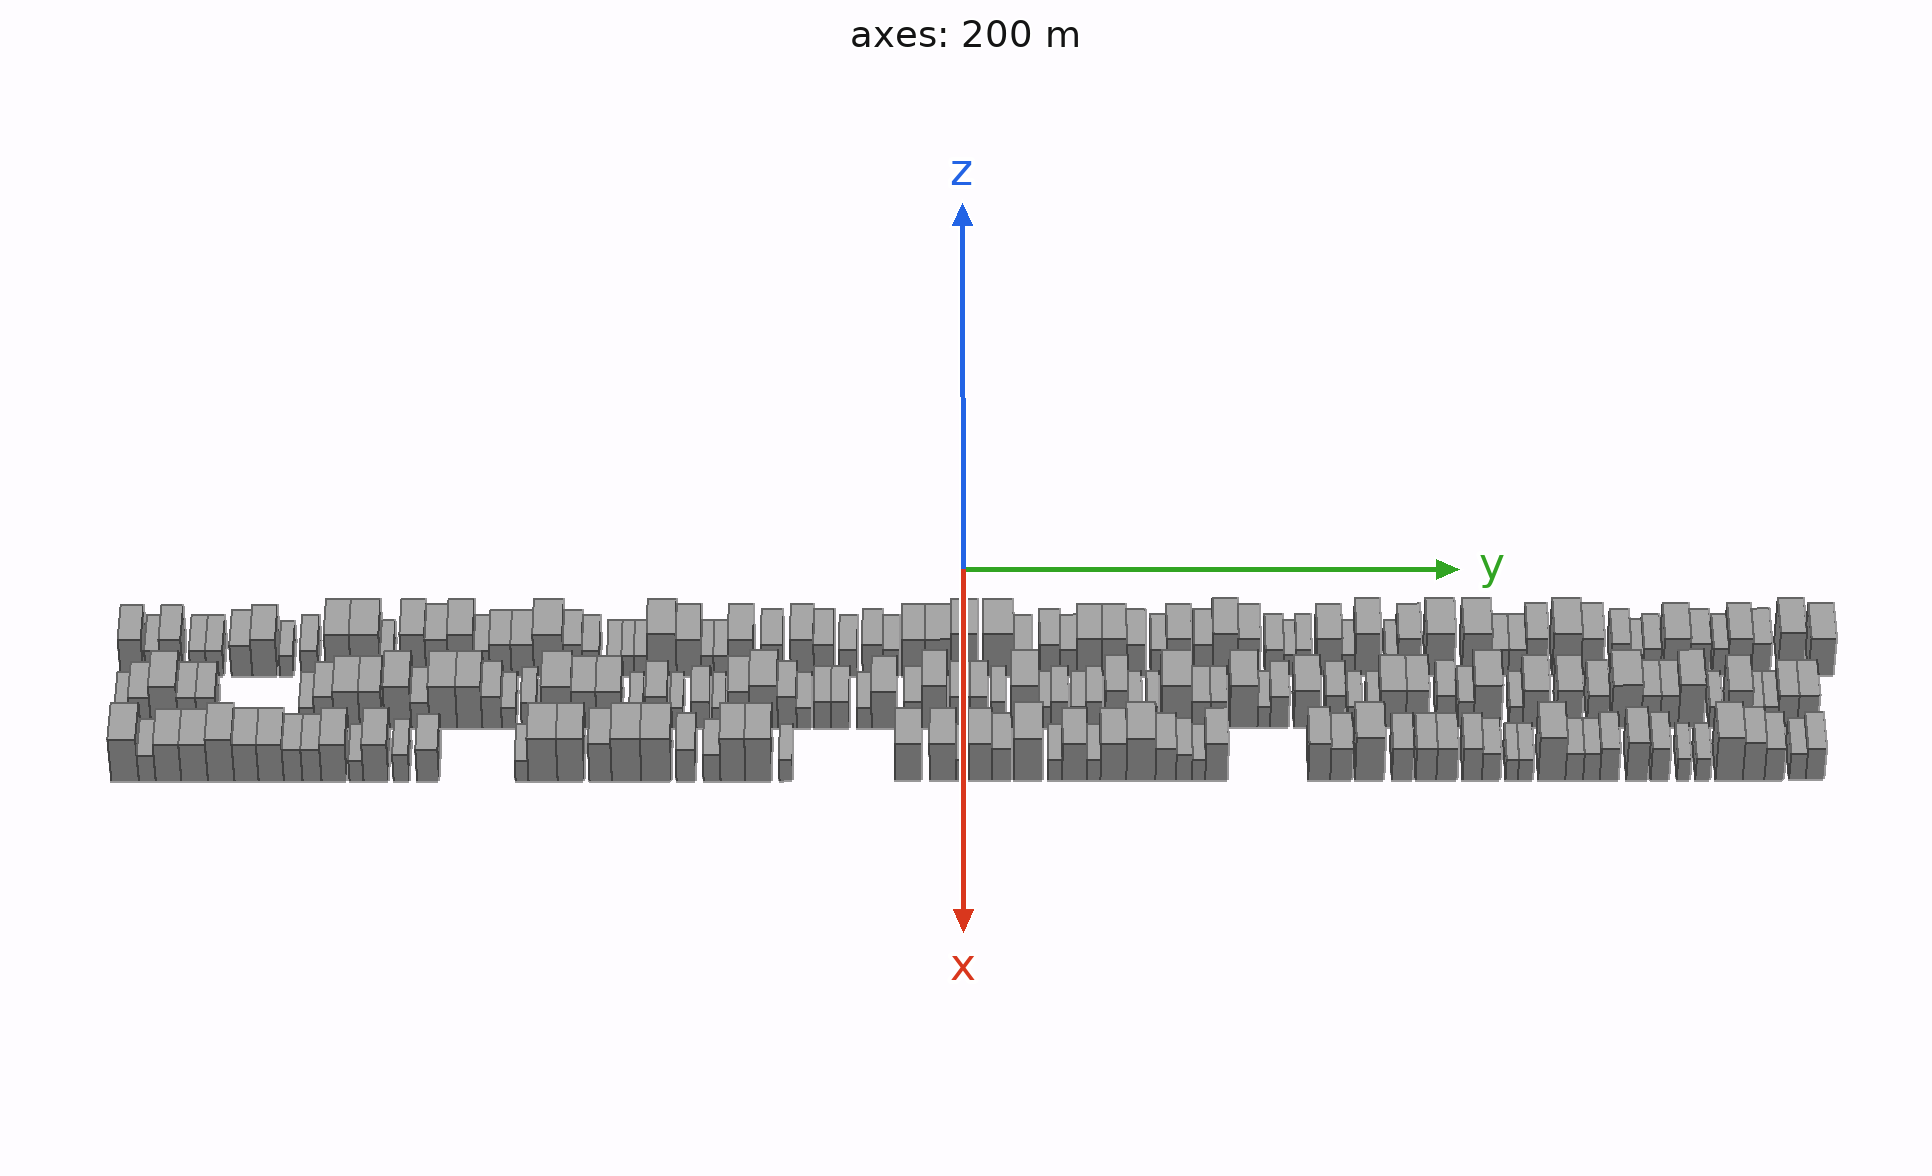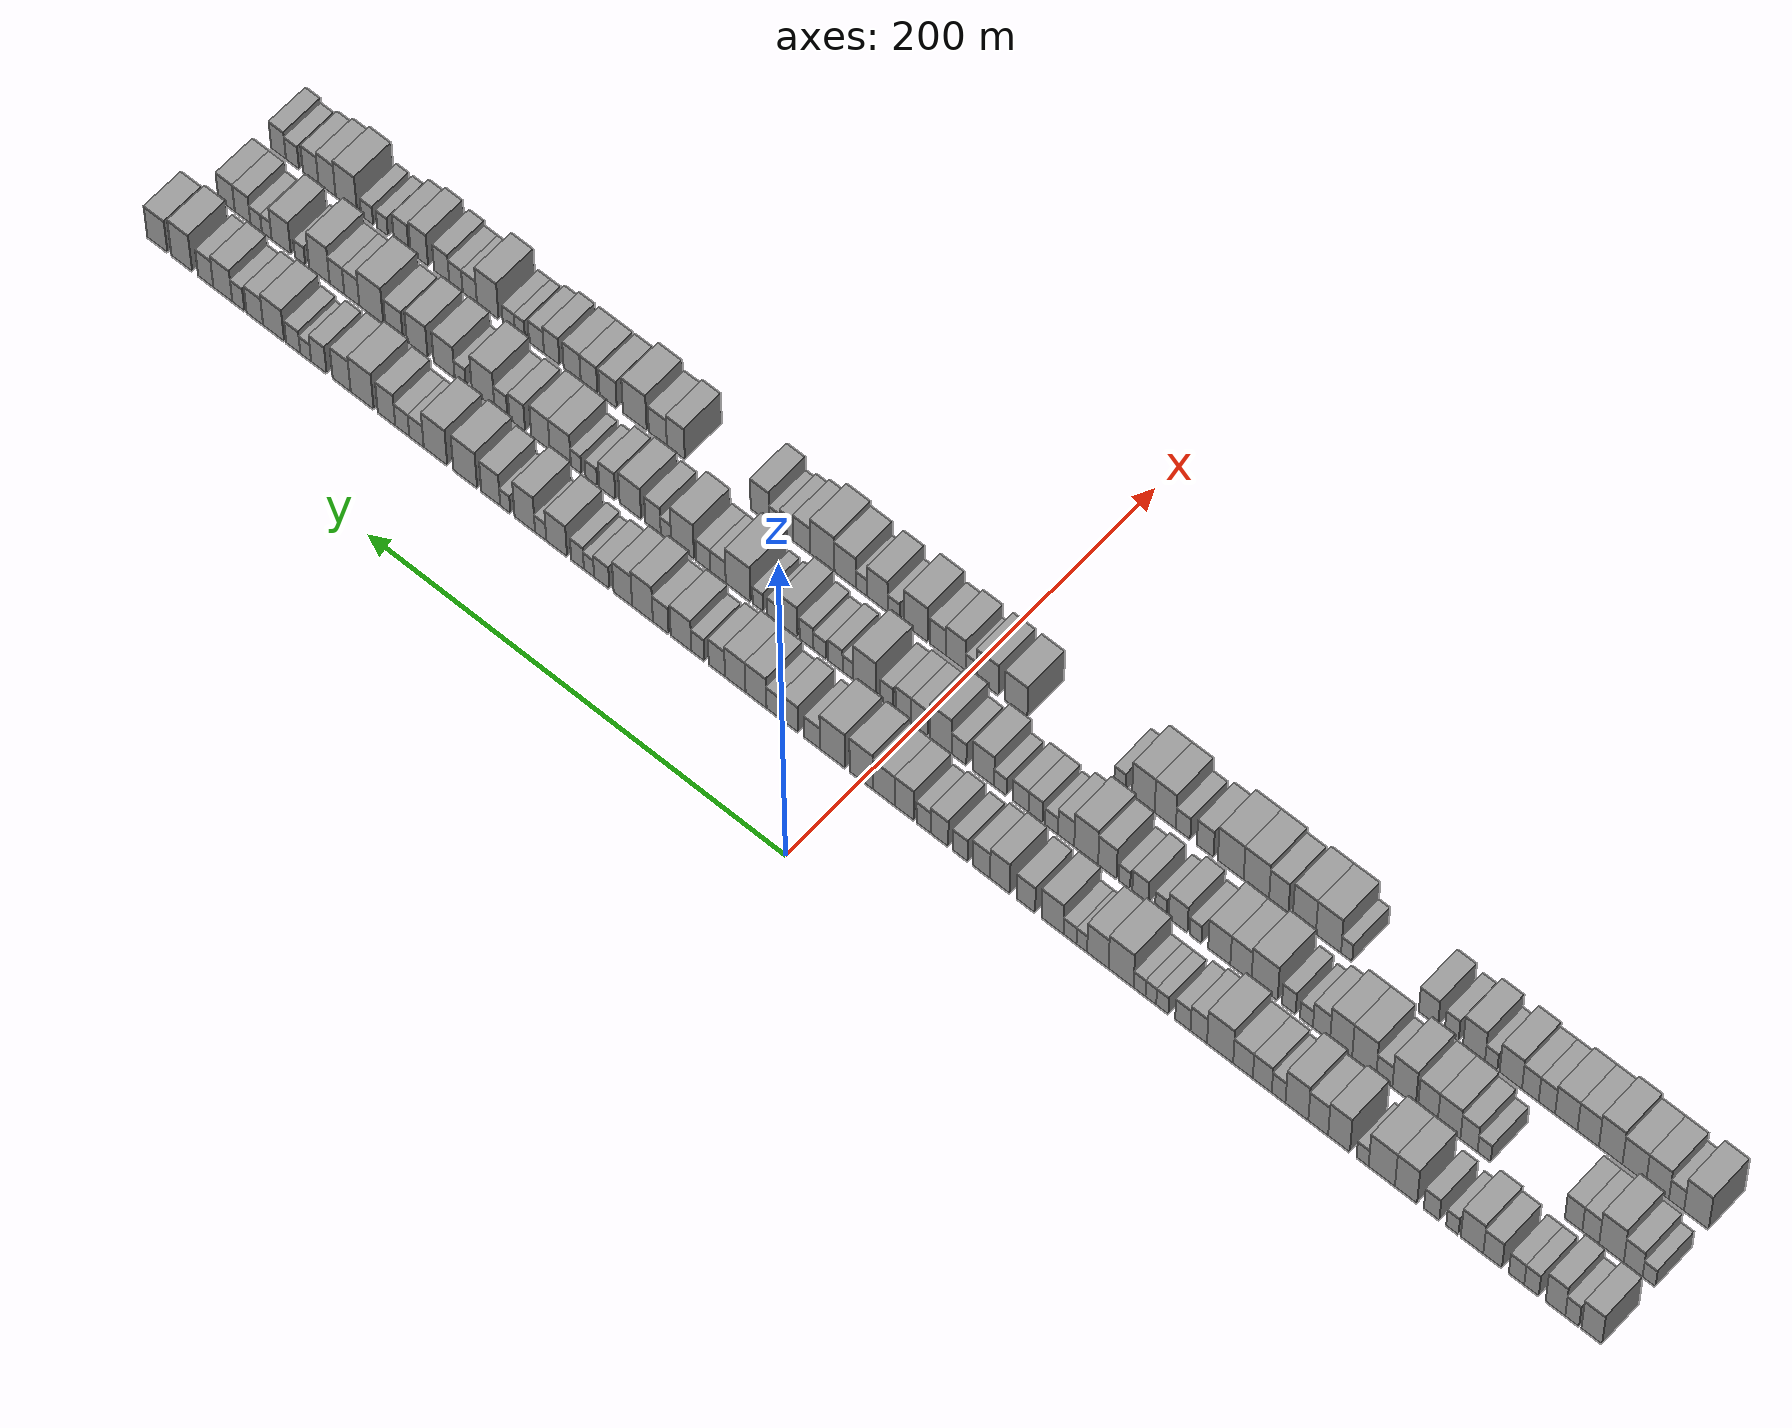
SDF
<sdf version="1.6">
 <world name="default">
  <scene>
   <sky><clouds><speed>12</speed></clouds></sky>
   <ambient>0.4 0.4 0.4 1</ambient>
   <background>0.7 0.7 0.7 1</background>
   <shadows>1</shadows>
  </scene>
  <gravity>0 0 -9.8066</gravity>
  <magnetic_field>6e-06 2.3e-05 -4.2e-05</magnetic_field>
  <physics default="0" name="default_physics" type="ode">
   <ode>
    <solver>
     <type>quick</type>
     <iters>10</iters>
     <sor>1.0</sor>
     <use_dynamic_moi_rescaling>0</use_dynamic_moi_rescaling>
    </solver>
    <constraints>
     <cfm>0</cfm>
     <erp>0.2</erp>
     <contact_max_correcting_vel>100</contact_max_correcting_vel>
     <contact_surface_layer>0.001</contact_surface_layer>
    </constraints>
   </ode>
   <max_step_size>0.004</max_step_size>
   <real_time_factor>1</real_time_factor>
   <real_time_update_rate>250</real_time_update_rate>
  </physics>
  <light name="sun" type="directional">
   <pose>0 0 10 0 0 0</pose>
   <diffuse>0.8 0.8 0.8 1</diffuse>
   <specular>0.2 0.2 0.2 1</specular>
   <attenuation>
    <range>1000</range>
    <constant>0.9</constant>
    <linear>0.01</linear>
    <quadratic>0.001</quadratic>
   </attenuation>
   <direction>-0.5 0.1 -0.9</direction>
  </light>
  <model name="building_1">
   <static>1</static>
   <pose>50.0000 -331.4374 0 0.000000 0.000000 0.000000</pose>
   <link name="link">
    <pose>0 0 10.50 0 0 0</pose>
    <collision name="collision"><geometry><box><size>20.0000 9.1252 21.0000</size></box></geometry></collision>
    <visual name="visual">
     <cast_shadows>0</cast_shadows>
     <geometry><box><size>20.0000 9.1252 21.0000</size></box></geometry>
     <material>
      <script>
       <uri>model://grey_wall/materials/scripts</uri>
       <uri>model://grey_wall/materials/textures</uri>
       <name>vrc/grey_wall</name>
      </script>
     </material>
    </visual>
   </link>
  </model>
  <model name="building_2">
   <static>1</static>
   <pose>50.0000 -322.8205 0 0.000000 0.000000 0.000000</pose>
   <link name="link">
    <pose>0 0 7.50 0 0 0</pose>
    <collision name="collision"><geometry><box><size>20.0000 6.1086 15.0000</size></box></geometry></collision>
    <visual name="visual">
     <cast_shadows>0</cast_shadows>
     <geometry><box><size>20.0000 6.1086 15.0000</size></box></geometry>
     <material>
      <script>
       <uri>model://grey_wall/materials/scripts</uri>
       <uri>model://grey_wall/materials/textures</uri>
       <name>vrc/grey_wall</name>
      </script>
     </material>
    </visual>
   </link>
  </model>
  <model name="building_3">
   <static>1</static>
   <pose>50.0000 -315.4396 0 0.000000 0.000000 0.000000</pose>
   <link name="link">
    <pose>0 0 10.50 0 0 0</pose>
    <collision name="collision"><geometry><box><size>20.0000 8.6531 21.0000</size></box></geometry></collision>
    <visual name="visual">
     <cast_shadows>0</cast_shadows>
     <geometry><box><size>20.0000 8.6531 21.0000</size></box></geometry>
     <material>
      <script>
       <uri>model://grey_wall/materials/scripts</uri>
       <uri>model://grey_wall/materials/textures</uri>
       <name>vrc/grey_wall</name>
      </script>
     </material>
    </visual>
   </link>
  </model>
  <model name="building_4">
   <static>1</static>
   <pose>50.0000 -304.8928 0 0.000000 0.000000 0.000000</pose>
   <link name="link">
    <pose>0 0 7.50 0 0 0</pose>
    <collision name="collision"><geometry><box><size>20.0000 6.4405 15.0000</size></box></geometry></collision>
    <visual name="visual">
     <cast_shadows>0</cast_shadows>
     <geometry><box><size>20.0000 6.4405 15.0000</size></box></geometry>
     <material>
      <script>
       <uri>model://grey_wall/materials/scripts</uri>
       <uri>model://grey_wall/materials/textures</uri>
       <name>vrc/grey_wall</name>
      </script>
     </material>
    </visual>
   </link>
  </model>
  <model name="building_5">
   <static>1</static>
   <pose>50.0000 -298.2574 0 0.000000 0.000000 0.000000</pose>
   <link name="link">
    <pose>0 0 7.50 0 0 0</pose>
    <collision name="collision"><geometry><box><size>20.0000 6.8302 15.0000</size></box></geometry></collision>
    <visual name="visual">
     <cast_shadows>0</cast_shadows>
     <geometry><box><size>20.0000 6.8302 15.0000</size></box></geometry>
     <material>
      <script>
       <uri>model://grey_wall/materials/scripts</uri>
       <uri>model://grey_wall/materials/textures</uri>
       <name>vrc/grey_wall</name>
      </script>
     </material>
    </visual>
   </link>
  </model>
  <model name="building_6">
   <static>1</static>
   <pose>50.0000 -287.6913 0 0.000000 0.000000 0.000000</pose>
   <link name="link">
    <pose>0 0 9.00 0 0 0</pose>
    <collision name="collision"><geometry><box><size>20.0000 8.3021 18.0000</size></box></geometry></collision>
    <visual name="visual">
     <cast_shadows>0</cast_shadows>
     <geometry><box><size>20.0000 8.3021 18.0000</size></box></geometry>
     <material>
      <script>
       <uri>model://grey_wall/materials/scripts</uri>
       <uri>model://grey_wall/materials/textures</uri>
       <name>vrc/grey_wall</name>
      </script>
     </material>
    </visual>
   </link>
  </model>
  <model name="building_7">
   <static>1</static>
   <pose>50.0000 -278.5388 0 0.000000 0.000000 0.000000</pose>
   <link name="link">
    <pose>0 0 10.50 0 0 0</pose>
    <collision name="collision"><geometry><box><size>20.0000 10.0028 21.0000</size></box></geometry></collision>
    <visual name="visual">
     <cast_shadows>0</cast_shadows>
     <geometry><box><size>20.0000 10.0028 21.0000</size></box></geometry>
     <material>
      <script>
       <uri>model://grey_wall/materials/scripts</uri>
       <uri>model://grey_wall/materials/textures</uri>
       <name>vrc/grey_wall</name>
      </script>
     </material>
    </visual>
   </link>
  </model>
  <model name="building_8">
   <static>1</static>
   <pose>50.0000 -269.7863 0 0.000000 0.000000 0.000000</pose>
   <link name="link">
    <pose>0 0 6.00 0 0 0</pose>
    <collision name="collision"><geometry><box><size>20.0000 5.5023 12.0000</size></box></geometry></collision>
    <visual name="visual">
     <cast_shadows>0</cast_shadows>
     <geometry><box><size>20.0000 5.5023 12.0000</size></box></geometry>
     <material>
      <script>
       <uri>model://grey_wall/materials/scripts</uri>
       <uri>model://grey_wall/materials/textures</uri>
       <name>vrc/grey_wall</name>
      </script>
     </material>
    </visual>
   </link>
  </model>
  <model name="building_9">
   <static>1</static>
   <pose>50.0000 -260.5613 0 0.000000 0.000000 0.000000</pose>
   <link name="link">
    <pose>0 0 7.50 0 0 0</pose>
    <collision name="collision"><geometry><box><size>20.0000 6.9476 15.0000</size></box></geometry></collision>
    <visual name="visual">
     <cast_shadows>0</cast_shadows>
     <geometry><box><size>20.0000 6.9476 15.0000</size></box></geometry>
     <material>
      <script>
       <uri>model://grey_wall/materials/scripts</uri>
       <uri>model://grey_wall/materials/textures</uri>
       <name>vrc/grey_wall</name>
      </script>
     </material>
    </visual>
   </link>
  </model>
  <model name="building_10">
   <static>1</static>
   <pose>50.0000 -249.1373 0 0.000000 0.000000 0.000000</pose>
   <link name="link">
    <pose>0 0 12.00 0 0 0</pose>
    <collision name="collision"><geometry><box><size>20.0000 9.9005 24.0000</size></box></geometry></collision>
    <visual name="visual">
     <cast_shadows>0</cast_shadows>
     <geometry><box><size>20.0000 9.9005 24.0000</size></box></geometry>
     <material>
      <script>
       <uri>model://grey_wall/materials/scripts</uri>
       <uri>model://grey_wall/materials/textures</uri>
       <name>vrc/grey_wall</name>
      </script>
     </material>
    </visual>
   </link>
  </model>
  <model name="building_11">
   <static>1</static>
   <pose>50.0000 -238.2753 0 0.000000 0.000000 0.000000</pose>
   <link name="link">
    <pose>0 0 12.00 0 0 0</pose>
    <collision name="collision"><geometry><box><size>20.0000 11.8236 24.0000</size></box></geometry></collision>
    <visual name="visual">
     <cast_shadows>0</cast_shadows>
     <geometry><box><size>20.0000 11.8236 24.0000</size></box></geometry>
     <material>
      <script>
       <uri>model://grey_wall/materials/scripts</uri>
       <uri>model://grey_wall/materials/textures</uri>
       <name>vrc/grey_wall</name>
      </script>
     </material>
    </visual>
   </link>
  </model>
  <model name="building_12">
   <static>1</static>
   <pose>50.0000 -229.6843 0 0.000000 0.000000 0.000000</pose>
   <link name="link">
    <pose>0 0 6.00 0 0 0</pose>
    <collision name="collision"><geometry><box><size>20.0000 5.3582 12.0000</size></box></geometry></collision>
    <visual name="visual">
     <cast_shadows>0</cast_shadows>
     <geometry><box><size>20.0000 5.3582 12.0000</size></box></geometry>
     <material>
      <script>
       <uri>model://grey_wall/materials/scripts</uri>
       <uri>model://grey_wall/materials/textures</uri>
       <name>vrc/grey_wall</name>
      </script>
     </material>
    </visual>
   </link>
  </model>
  <model name="building_13">
   <static>1</static>
   <pose>50.0000 -219.1030 0 0.000000 0.000000 0.000000</pose>
   <link name="link">
    <pose>0 0 12.00 0 0 0</pose>
    <collision name="collision"><geometry><box><size>20.0000 9.8044 24.0000</size></box></geometry></collision>
    <visual name="visual">
     <cast_shadows>0</cast_shadows>
     <geometry><box><size>20.0000 9.8044 24.0000</size></box></geometry>
     <material>
      <script>
       <uri>model://grey_wall/materials/scripts</uri>
       <uri>model://grey_wall/materials/textures</uri>
       <name>vrc/grey_wall</name>
      </script>
     </material>
    </visual>
   </link>
  </model>
  <model name="building_14">
   <static>1</static>
   <pose>50.0000 -209.7361 0 0.000000 0.000000 0.000000</pose>
   <link name="link">
    <pose>0 0 10.50 0 0 0</pose>
    <collision name="collision"><geometry><box><size>20.0000 8.9294 21.0000</size></box></geometry></collision>
    <visual name="visual">
     <cast_shadows>0</cast_shadows>
     <geometry><box><size>20.0000 8.9294 21.0000</size></box></geometry>
     <material>
      <script>
       <uri>model://grey_wall/materials/scripts</uri>
       <uri>model://grey_wall/materials/textures</uri>
       <name>vrc/grey_wall</name>
      </script>
     </material>
    </visual>
   </link>
  </model>
  <model name="building_15">
   <static>1</static>
   <pose>50.0000 -200.1119 0 0.000000 0.000000 0.000000</pose>
   <link name="link">
    <pose>0 0 12.00 0 0 0</pose>
    <collision name="collision"><geometry><box><size>20.0000 10.3190 24.0000</size></box></geometry></collision>
    <visual name="visual">
     <cast_shadows>0</cast_shadows>
     <geometry><box><size>20.0000 10.3190 24.0000</size></box></geometry>
     <material>
      <script>
       <uri>model://grey_wall/materials/scripts</uri>
       <uri>model://grey_wall/materials/textures</uri>
       <name>vrc/grey_wall</name>
      </script>
     </material>
    </visual>
   </link>
  </model>
  <model name="building_16">
   <static>1</static>
   <pose>50.0000 -191.8683 0 0.000000 0.000000 0.000000</pose>
   <link name="link">
    <pose>0 0 7.50 0 0 0</pose>
    <collision name="collision"><geometry><box><size>20.0000 6.1682 15.0000</size></box></geometry></collision>
    <visual name="visual">
     <cast_shadows>0</cast_shadows>
     <geometry><box><size>20.0000 6.1682 15.0000</size></box></geometry>
     <material>
      <script>
       <uri>model://grey_wall/materials/scripts</uri>
       <uri>model://grey_wall/materials/textures</uri>
       <name>vrc/grey_wall</name>
      </script>
     </material>
    </visual>
   </link>
  </model>
  <model name="building_17">
   <static>1</static>
   <pose>50.0000 -184.5009 0 0.000000 0.000000 0.000000</pose>
   <link name="link">
    <pose>0 0 9.00 0 0 0</pose>
    <collision name="collision"><geometry><box><size>20.0000 8.5665 18.0000</size></box></geometry></collision>
    <visual name="visual">
     <cast_shadows>0</cast_shadows>
     <geometry><box><size>20.0000 8.5665 18.0000</size></box></geometry>
     <material>
      <script>
       <uri>model://grey_wall/materials/scripts</uri>
       <uri>model://grey_wall/materials/textures</uri>
       <name>vrc/grey_wall</name>
      </script>
     </material>
    </visual>
   </link>
  </model>
  <model name="building_18">
   <static>1</static>
   <pose>50.0000 -175.7583 0 0.000000 0.000000 0.000000</pose>
   <link name="link">
    <pose>0 0 9.00 0 0 0</pose>
    <collision name="collision"><geometry><box><size>20.0000 8.9187 18.0000</size></box></geometry></collision>
    <visual name="visual">
     <cast_shadows>0</cast_shadows>
     <geometry><box><size>20.0000 8.9187 18.0000</size></box></geometry>
     <material>
      <script>
       <uri>model://grey_wall/materials/scripts</uri>
       <uri>model://grey_wall/materials/textures</uri>
       <name>vrc/grey_wall</name>
      </script>
     </material>
    </visual>
   </link>
  </model>
  <model name="building_19">
   <static>1</static>
   <pose>50.0000 -165.3610 0 0.000000 0.000000 0.000000</pose>
   <link name="link">
    <pose>0 0 12.00 0 0 0</pose>
    <collision name="collision"><geometry><box><size>20.0000 11.8758 24.0000</size></box></geometry></collision>
    <visual name="visual">
     <cast_shadows>0</cast_shadows>
     <geometry><box><size>20.0000 11.8758 24.0000</size></box></geometry>
     <material>
      <script>
       <uri>model://grey_wall/materials/scripts</uri>
       <uri>model://grey_wall/materials/textures</uri>
       <name>vrc/grey_wall</name>
      </script>
     </material>
    </visual>
   </link>
  </model>
  <model name="building_20">
   <static>1</static>
   <pose>50.0000 -155.6703 0 0.000000 0.000000 0.000000</pose>
   <link name="link">
    <pose>0 0 9.00 0 0 0</pose>
    <collision name="collision"><geometry><box><size>20.0000 7.5056 18.0000</size></box></geometry></collision>
    <visual name="visual">
     <cast_shadows>0</cast_shadows>
     <geometry><box><size>20.0000 7.5056 18.0000</size></box></geometry>
     <material>
      <script>
       <uri>model://grey_wall/materials/scripts</uri>
       <uri>model://grey_wall/materials/textures</uri>
       <name>vrc/grey_wall</name>
      </script>
     </material>
    </visual>
   </link>
  </model>
  <model name="building_21">
   <static>1</static>
   <pose>50.0000 -148.4267 0 0.000000 0.000000 0.000000</pose>
   <link name="link">
    <pose>0 0 7.50 0 0 0</pose>
    <collision name="collision"><geometry><box><size>20.0000 6.9815 15.0000</size></box></geometry></collision>
    <visual name="visual">
     <cast_shadows>0</cast_shadows>
     <geometry><box><size>20.0000 6.9815 15.0000</size></box></geometry>
     <material>
      <script>
       <uri>model://grey_wall/materials/scripts</uri>
       <uri>model://grey_wall/materials/textures</uri>
       <name>vrc/grey_wall</name>
      </script>
     </material>
    </visual>
   </link>
  </model>
  <model name="building_22">
   <static>1</static>
   <pose>50.0000 -139.1148 0 0.000000 0.000000 0.000000</pose>
   <link name="link">
    <pose>0 0 6.00 0 0 0</pose>
    <collision name="collision"><geometry><box><size>20.0000 5.6423 12.0000</size></box></geometry></collision>
    <visual name="visual">
     <cast_shadows>0</cast_shadows>
     <geometry><box><size>20.0000 5.6423 12.0000</size></box></geometry>
     <material>
      <script>
       <uri>model://grey_wall/materials/scripts</uri>
       <uri>model://grey_wall/materials/textures</uri>
       <name>vrc/grey_wall</name>
      </script>
     </material>
    </visual>
   </link>
  </model>
  <model name="building_23">
   <static>1</static>
   <pose>50.0000 -133.8215 0 0.000000 0.000000 0.000000</pose>
   <link name="link">
    <pose>0 0 6.00 0 0 0</pose>
    <collision name="collision"><geometry><box><size>20.0000 4.9443 12.0000</size></box></geometry></collision>
    <visual name="visual">
     <cast_shadows>0</cast_shadows>
     <geometry><box><size>20.0000 4.9443 12.0000</size></box></geometry>
     <material>
      <script>
       <uri>model://grey_wall/materials/scripts</uri>
       <uri>model://grey_wall/materials/textures</uri>
       <name>vrc/grey_wall</name>
      </script>
     </material>
    </visual>
   </link>
  </model>
  <model name="building_24">
   <static>1</static>
   <pose>50.0000 -128.6585 0 0.000000 0.000000 0.000000</pose>
   <link name="link">
    <pose>0 0 6.00 0 0 0</pose>
    <collision name="collision"><geometry><box><size>20.0000 5.3816 12.0000</size></box></geometry></collision>
    <visual name="visual">
     <cast_shadows>0</cast_shadows>
     <geometry><box><size>20.0000 5.3816 12.0000</size></box></geometry>
     <material>
      <script>
       <uri>model://grey_wall/materials/scripts</uri>
       <uri>model://grey_wall/materials/textures</uri>
       <name>vrc/grey_wall</name>
      </script>
     </material>
    </visual>
   </link>
  </model>
  <model name="building_25">
   <static>1</static>
   <pose>50.0000 -120.2226 0 0.000000 0.000000 0.000000</pose>
   <link name="link">
    <pose>0 0 12.00 0 0 0</pose>
    <collision name="collision"><geometry><box><size>20.0000 11.4903 24.0000</size></box></geometry></collision>
    <visual name="visual">
     <cast_shadows>0</cast_shadows>
     <geometry><box><size>20.0000 11.4903 24.0000</size></box></geometry>
     <material>
      <script>
       <uri>model://grey_wall/materials/scripts</uri>
       <uri>model://grey_wall/materials/textures</uri>
       <name>vrc/grey_wall</name>
      </script>
     </material>
    </visual>
   </link>
  </model>
  <model name="building_26">
   <static>1</static>
   <pose>50.0000 -109.5448 0 0.000000 0.000000 0.000000</pose>
   <link name="link">
    <pose>0 0 10.50 0 0 0</pose>
    <collision name="collision"><geometry><box><size>20.0000 9.8654 21.0000</size></box></geometry></collision>
    <visual name="visual">
     <cast_shadows>0</cast_shadows>
     <geometry><box><size>20.0000 9.8654 21.0000</size></box></geometry>
     <material>
      <script>
       <uri>model://grey_wall/materials/scripts</uri>
       <uri>model://grey_wall/materials/textures</uri>
       <name>vrc/grey_wall</name>
      </script>
     </material>
    </visual>
   </link>
  </model>
  <model name="building_27">
   <static>1</static>
   <pose>50.0000 -102.1671 0 0.000000 0.000000 0.000000</pose>
   <link name="link">
    <pose>0 0 6.00 0 0 0</pose>
    <collision name="collision"><geometry><box><size>20.0000 4.8900 12.0000</size></box></geometry></collision>
    <visual name="visual">
     <cast_shadows>0</cast_shadows>
     <geometry><box><size>20.0000 4.8900 12.0000</size></box></geometry>
     <material>
      <script>
       <uri>model://grey_wall/materials/scripts</uri>
       <uri>model://grey_wall/materials/textures</uri>
       <name>vrc/grey_wall</name>
      </script>
     </material>
    </visual>
   </link>
  </model>
  <model name="building_28">
   <static>1</static>
   <pose>50.0000 -96.7376 0 0.000000 0.000000 0.000000</pose>
   <link name="link">
    <pose>0 0 6.00 0 0 0</pose>
    <collision name="collision"><geometry><box><size>20.0000 5.9690 12.0000</size></box></geometry></collision>
    <visual name="visual">
     <cast_shadows>0</cast_shadows>
     <geometry><box><size>20.0000 5.9690 12.0000</size></box></geometry>
     <material>
      <script>
       <uri>model://grey_wall/materials/scripts</uri>
       <uri>model://grey_wall/materials/textures</uri>
       <name>vrc/grey_wall</name>
      </script>
     </material>
    </visual>
   </link>
  </model>
  <model name="building_29">
   <static>1</static>
   <pose>50.0000 -88.7289 0 0.000000 0.000000 0.000000</pose>
   <link name="link">
    <pose>0 0 10.50 0 0 0</pose>
    <collision name="collision"><geometry><box><size>20.0000 10.0484 21.0000</size></box></geometry></collision>
    <visual name="visual">
     <cast_shadows>0</cast_shadows>
     <geometry><box><size>20.0000 10.0484 21.0000</size></box></geometry>
     <material>
      <script>
       <uri>model://grey_wall/materials/scripts</uri>
       <uri>model://grey_wall/materials/textures</uri>
       <name>vrc/grey_wall</name>
      </script>
     </material>
    </visual>
   </link>
  </model>
  <model name="building_30">
   <static>1</static>
   <pose>50.0000 -76.3814 0 0.000000 0.000000 0.000000</pose>
   <link name="link">
    <pose>0 0 9.00 0 0 0</pose>
    <collision name="collision"><geometry><box><size>20.0000 8.6467 18.0000</size></box></geometry></collision>
    <visual name="visual">
     <cast_shadows>0</cast_shadows>
     <geometry><box><size>20.0000 8.6467 18.0000</size></box></geometry>
     <material>
      <script>
       <uri>model://grey_wall/materials/scripts</uri>
       <uri>model://grey_wall/materials/textures</uri>
       <name>vrc/grey_wall</name>
      </script>
     </material>
    </visual>
   </link>
  </model>
  <model name="building_31">
   <static>1</static>
   <pose>50.0000 -64.4616 0 0.000000 0.000000 0.000000</pose>
   <link name="link">
    <pose>0 0 10.50 0 0 0</pose>
    <collision name="collision"><geometry><box><size>20.0000 9.1930 21.0000</size></box></geometry></collision>
    <visual name="visual">
     <cast_shadows>0</cast_shadows>
     <geometry><box><size>20.0000 9.1930 21.0000</size></box></geometry>
     <material>
      <script>
       <uri>model://grey_wall/materials/scripts</uri>
       <uri>model://grey_wall/materials/textures</uri>
       <name>vrc/grey_wall</name>
      </script>
     </material>
    </visual>
   </link>
  </model>
  <model name="building_32">
   <static>1</static>
   <pose>50.0000 -55.7582 0 0.000000 0.000000 0.000000</pose>
   <link name="link">
    <pose>0 0 9.00 0 0 0</pose>
    <collision name="collision"><geometry><box><size>20.0000 8.2138 18.0000</size></box></geometry></collision>
    <visual name="visual">
     <cast_shadows>0</cast_shadows>
     <geometry><box><size>20.0000 8.2138 18.0000</size></box></geometry>
     <material>
      <script>
       <uri>model://grey_wall/materials/scripts</uri>
       <uri>model://grey_wall/materials/textures</uri>
       <name>vrc/grey_wall</name>
      </script>
     </material>
    </visual>
   </link>
  </model>
  <model name="building_33">
   <static>1</static>
   <pose>50.0000 -46.0465 0 0.000000 0.000000 0.000000</pose>
   <link name="link">
    <pose>0 0 7.50 0 0 0</pose>
    <collision name="collision"><geometry><box><size>20.0000 7.2096 15.0000</size></box></geometry></collision>
    <visual name="visual">
     <cast_shadows>0</cast_shadows>
     <geometry><box><size>20.0000 7.2096 15.0000</size></box></geometry>
     <material>
      <script>
       <uri>model://grey_wall/materials/scripts</uri>
       <uri>model://grey_wall/materials/textures</uri>
       <name>vrc/grey_wall</name>
      </script>
     </material>
    </visual>
   </link>
  </model>
  <model name="building_34">
   <static>1</static>
   <pose>50.0000 -36.3242 0 0.000000 0.000000 0.000000</pose>
   <link name="link">
    <pose>0 0 9.00 0 0 0</pose>
    <collision name="collision"><geometry><box><size>20.0000 8.2350 18.0000</size></box></geometry></collision>
    <visual name="visual">
     <cast_shadows>0</cast_shadows>
     <geometry><box><size>20.0000 8.2350 18.0000</size></box></geometry>
     <material>
      <script>
       <uri>model://grey_wall/materials/scripts</uri>
       <uri>model://grey_wall/materials/textures</uri>
       <name>vrc/grey_wall</name>
      </script>
     </material>
    </visual>
   </link>
  </model>
  <model name="building_35">
   <static>1</static>
   <pose>50.0000 -28.8858 0 0.000000 0.000000 0.000000</pose>
   <link name="link">
    <pose>0 0 7.50 0 0 0</pose>
    <collision name="collision"><geometry><box><size>20.0000 6.6417 15.0000</size></box></geometry></collision>
    <visual name="visual">
     <cast_shadows>0</cast_shadows>
     <geometry><box><size>20.0000 6.6417 15.0000</size></box></geometry>
     <material>
      <script>
       <uri>model://grey_wall/materials/scripts</uri>
       <uri>model://grey_wall/materials/textures</uri>
       <name>vrc/grey_wall</name>
      </script>
     </material>
    </visual>
   </link>
  </model>
  <model name="building_36">
   <static>1</static>
   <pose>50.0000 -20.0085 0 0.000000 0.000000 0.000000</pose>
   <link name="link">
    <pose>0 0 10.50 0 0 0</pose>
    <collision name="collision"><geometry><box><size>20.0000 9.1130 21.0000</size></box></geometry></collision>
    <visual name="visual">
     <cast_shadows>0</cast_shadows>
     <geometry><box><size>20.0000 9.1130 21.0000</size></box></geometry>
     <material>
      <script>
       <uri>model://grey_wall/materials/scripts</uri>
       <uri>model://grey_wall/materials/textures</uri>
       <name>vrc/grey_wall</name>
      </script>
     </material>
    </visual>
   </link>
  </model>
  <model name="building_37">
   <static>1</static>
   <pose>50.0000 -10.3064 0 0.000000 0.000000 0.000000</pose>
   <link name="link">
    <pose>0 0 10.50 0 0 0</pose>
    <collision name="collision"><geometry><box><size>20.0000 10.2912 21.0000</size></box></geometry></collision>
    <visual name="visual">
     <cast_shadows>0</cast_shadows>
     <geometry><box><size>20.0000 10.2912 21.0000</size></box></geometry>
     <material>
      <script>
       <uri>model://grey_wall/materials/scripts</uri>
       <uri>model://grey_wall/materials/textures</uri>
       <name>vrc/grey_wall</name>
      </script>
     </material>
    </visual>
   </link>
  </model>
  <model name="building_38">
   <static>1</static>
   <pose>50.0000 0.2645 0 0.000000 0.000000 0.000000</pose>
   <link name="link">
    <pose>0 0 12.00 0 0 0</pose>
    <collision name="collision"><geometry><box><size>20.0000 10.8505 24.0000</size></box></geometry></collision>
    <visual name="visual">
     <cast_shadows>0</cast_shadows>
     <geometry><box><size>20.0000 10.8505 24.0000</size></box></geometry>
     <material>
      <script>
       <uri>model://grey_wall/materials/scripts</uri>
       <uri>model://grey_wall/materials/textures</uri>
       <name>vrc/grey_wall</name>
      </script>
     </material>
    </visual>
   </link>
  </model>
  <model name="building_39">
   <static>1</static>
   <pose>50.0000 13.6793 0 0.000000 0.000000 0.000000</pose>
   <link name="link">
    <pose>0 0 12.00 0 0 0</pose>
    <collision name="collision"><geometry><box><size>20.0000 11.9791 24.0000</size></box></geometry></collision>
    <visual name="visual">
     <cast_shadows>0</cast_shadows>
     <geometry><box><size>20.0000 11.9791 24.0000</size></box></geometry>
     <material>
      <script>
       <uri>model://grey_wall/materials/scripts</uri>
       <uri>model://grey_wall/materials/textures</uri>
       <name>vrc/grey_wall</name>
      </script>
     </material>
    </visual>
   </link>
  </model>
  <model name="building_40">
   <static>1</static>
   <pose>50.0000 23.3545 0 0.000000 0.000000 0.000000</pose>
   <link name="link">
    <pose>0 0 7.50 0 0 0</pose>
    <collision name="collision"><geometry><box><size>20.0000 7.3714 15.0000</size></box></geometry></collision>
    <visual name="visual">
     <cast_shadows>0</cast_shadows>
     <geometry><box><size>20.0000 7.3714 15.0000</size></box></geometry>
     <material>
      <script>
       <uri>model://grey_wall/materials/scripts</uri>
       <uri>model://grey_wall/materials/textures</uri>
       <name>vrc/grey_wall</name>
      </script>
     </material>
    </visual>
   </link>
  </model>
  <model name="building_41">
   <static>1</static>
   <pose>50.0000 34.0789 0 0.000000 0.000000 0.000000</pose>
   <link name="link">
    <pose>0 0 9.00 0 0 0</pose>
    <collision name="collision"><geometry><box><size>20.0000 8.0774 18.0000</size></box></geometry></collision>
    <visual name="visual">
     <cast_shadows>0</cast_shadows>
     <geometry><box><size>20.0000 8.0774 18.0000</size></box></geometry>
     <material>
      <script>
       <uri>model://grey_wall/materials/scripts</uri>
       <uri>model://grey_wall/materials/textures</uri>
       <name>vrc/grey_wall</name>
      </script>
     </material>
    </visual>
   </link>
  </model>
  <model name="building_42">
   <static>1</static>
   <pose>50.0000 41.5247 0 0.000000 0.000000 0.000000</pose>
   <link name="link">
    <pose>0 0 7.50 0 0 0</pose>
    <collision name="collision"><geometry><box><size>20.0000 6.8142 15.0000</size></box></geometry></collision>
    <visual name="visual">
     <cast_shadows>0</cast_shadows>
     <geometry><box><size>20.0000 6.8142 15.0000</size></box></geometry>
     <material>
      <script>
       <uri>model://grey_wall/materials/scripts</uri>
       <uri>model://grey_wall/materials/textures</uri>
       <name>vrc/grey_wall</name>
      </script>
     </material>
    </visual>
   </link>
  </model>
  <model name="building_43">
   <static>1</static>
   <pose>50.0000 49.9054 0 0.000000 0.000000 0.000000</pose>
   <link name="link">
    <pose>0 0 10.50 0 0 0</pose>
    <collision name="collision"><geometry><box><size>20.0000 9.9473 21.0000</size></box></geometry></collision>
    <visual name="visual">
     <cast_shadows>0</cast_shadows>
     <geometry><box><size>20.0000 9.9473 21.0000</size></box></geometry>
     <material>
      <script>
       <uri>model://grey_wall/materials/scripts</uri>
       <uri>model://grey_wall/materials/textures</uri>
       <name>vrc/grey_wall</name>
      </script>
     </material>
    </visual>
   </link>
  </model>
  <model name="building_44">
   <static>1</static>
   <pose>50.0000 59.7354 0 0.000000 0.000000 0.000000</pose>
   <link name="link">
    <pose>0 0 10.50 0 0 0</pose>
    <collision name="collision"><geometry><box><size>20.0000 9.7126 21.0000</size></box></geometry></collision>
    <visual name="visual">
     <cast_shadows>0</cast_shadows>
     <geometry><box><size>20.0000 9.7126 21.0000</size></box></geometry>
     <material>
      <script>
       <uri>model://grey_wall/materials/scripts</uri>
       <uri>model://grey_wall/materials/textures</uri>
       <name>vrc/grey_wall</name>
      </script>
     </material>
    </visual>
   </link>
  </model>
  <model name="building_45">
   <static>1</static>
   <pose>50.0000 68.4710 0 0.000000 0.000000 0.000000</pose>
   <link name="link">
    <pose>0 0 9.00 0 0 0</pose>
    <collision name="collision"><geometry><box><size>20.0000 7.7587 18.0000</size></box></geometry></collision>
    <visual name="visual">
     <cast_shadows>0</cast_shadows>
     <geometry><box><size>20.0000 7.7587 18.0000</size></box></geometry>
     <material>
      <script>
       <uri>model://grey_wall/materials/scripts</uri>
       <uri>model://grey_wall/materials/textures</uri>
       <name>vrc/grey_wall</name>
      </script>
     </material>
    </visual>
   </link>
  </model>
  <model name="building_46">
   <static>1</static>
   <pose>50.0000 77.4622 0 0.000000 0.000000 0.000000</pose>
   <link name="link">
    <pose>0 0 7.50 0 0 0</pose>
    <collision name="collision"><geometry><box><size>20.0000 6.2238 15.0000</size></box></geometry></collision>
    <visual name="visual">
     <cast_shadows>0</cast_shadows>
     <geometry><box><size>20.0000 6.2238 15.0000</size></box></geometry>
     <material>
      <script>
       <uri>model://grey_wall/materials/scripts</uri>
       <uri>model://grey_wall/materials/textures</uri>
       <name>vrc/grey_wall</name>
      </script>
     </material>
    </visual>
   </link>
  </model>
  <model name="building_47">
   <static>1</static>
   <pose>50.0000 85.5248 0 0.000000 0.000000 0.000000</pose>
   <link name="link">
    <pose>0 0 10.50 0 0 0</pose>
    <collision name="collision"><geometry><box><size>20.0000 9.9014 21.0000</size></box></geometry></collision>
    <visual name="visual">
     <cast_shadows>0</cast_shadows>
     <geometry><box><size>20.0000 9.9014 21.0000</size></box></geometry>
     <material>
      <script>
       <uri>model://grey_wall/materials/scripts</uri>
       <uri>model://grey_wall/materials/textures</uri>
       <name>vrc/grey_wall</name>
      </script>
     </material>
    </visual>
   </link>
  </model>
  <model name="building_48">
   <static>1</static>
   <pose>50.0000 95.2247 0 0.000000 0.000000 0.000000</pose>
   <link name="link">
    <pose>0 0 9.00 0 0 0</pose>
    <collision name="collision"><geometry><box><size>20.0000 7.4985 18.0000</size></box></geometry></collision>
    <visual name="visual">
     <cast_shadows>0</cast_shadows>
     <geometry><box><size>20.0000 7.4985 18.0000</size></box></geometry>
     <material>
      <script>
       <uri>model://grey_wall/materials/scripts</uri>
       <uri>model://grey_wall/materials/textures</uri>
       <name>vrc/grey_wall</name>
      </script>
     </material>
    </visual>
   </link>
  </model>
  <model name="building_49">
   <static>1</static>
   <pose>50.0000 103.9581 0 0.000000 0.000000 0.000000</pose>
   <link name="link">
    <pose>0 0 12.00 0 0 0</pose>
    <collision name="collision"><geometry><box><size>20.0000 9.9683 24.0000</size></box></geometry></collision>
    <visual name="visual">
     <cast_shadows>0</cast_shadows>
     <geometry><box><size>20.0000 9.9683 24.0000</size></box></geometry>
     <material>
      <script>
       <uri>model://grey_wall/materials/scripts</uri>
       <uri>model://grey_wall/materials/textures</uri>
       <name>vrc/grey_wall</name>
      </script>
     </material>
    </visual>
   </link>
  </model>
  <model name="building_50">
   <static>1</static>
   <pose>50.0000 113.3928 0 0.000000 0.000000 0.000000</pose>
   <link name="link">
    <pose>0 0 10.50 0 0 0</pose>
    <collision name="collision"><geometry><box><size>20.0000 8.9011 21.0000</size></box></geometry></collision>
    <visual name="visual">
     <cast_shadows>0</cast_shadows>
     <geometry><box><size>20.0000 8.9011 21.0000</size></box></geometry>
     <material>
      <script>
       <uri>model://grey_wall/materials/scripts</uri>
       <uri>model://grey_wall/materials/textures</uri>
       <name>vrc/grey_wall</name>
      </script>
     </material>
    </visual>
   </link>
  </model>
  <model name="building_51">
   <static>1</static>
   <pose>50.0000 123.5174 0 0.000000 0.000000 0.000000</pose>
   <link name="link">
    <pose>0 0 7.50 0 0 0</pose>
    <collision name="collision"><geometry><box><size>20.0000 7.3481 15.0000</size></box></geometry></collision>
    <visual name="visual">
     <cast_shadows>0</cast_shadows>
     <geometry><box><size>20.0000 7.3481 15.0000</size></box></geometry>
     <material>
      <script>
       <uri>model://grey_wall/materials/scripts</uri>
       <uri>model://grey_wall/materials/textures</uri>
       <name>vrc/grey_wall</name>
      </script>
     </material>
    </visual>
   </link>
  </model>
  <model name="building_52">
   <static>1</static>
   <pose>50.0000 129.6561 0 0.000000 0.000000 0.000000</pose>
   <link name="link">
    <pose>0 0 6.00 0 0 0</pose>
    <collision name="collision"><geometry><box><size>20.0000 4.9293 12.0000</size></box></geometry></collision>
    <visual name="visual">
     <cast_shadows>0</cast_shadows>
     <geometry><box><size>20.0000 4.9293 12.0000</size></box></geometry>
     <material>
      <script>
       <uri>model://grey_wall/materials/scripts</uri>
       <uri>model://grey_wall/materials/textures</uri>
       <name>vrc/grey_wall</name>
      </script>
     </material>
    </visual>
   </link>
  </model>
  <model name="building_53">
   <static>1</static>
   <pose>50.0000 135.1810 0 0.000000 0.000000 0.000000</pose>
   <link name="link">
    <pose>0 0 7.50 0 0 0</pose>
    <collision name="collision"><geometry><box><size>20.0000 6.1205 15.0000</size></box></geometry></collision>
    <visual name="visual">
     <cast_shadows>0</cast_shadows>
     <geometry><box><size>20.0000 6.1205 15.0000</size></box></geometry>
     <material>
      <script>
       <uri>model://grey_wall/materials/scripts</uri>
       <uri>model://grey_wall/materials/textures</uri>
       <name>vrc/grey_wall</name>
      </script>
     </material>
    </visual>
   </link>
  </model>
  <model name="building_54">
   <static>1</static>
   <pose>50.0000 145.2424 0 0.000000 0.000000 0.000000</pose>
   <link name="link">
    <pose>0 0 10.50 0 0 0</pose>
    <collision name="collision"><geometry><box><size>20.0000 10.0023 21.0000</size></box></geometry></collision>
    <visual name="visual">
     <cast_shadows>0</cast_shadows>
     <geometry><box><size>20.0000 10.0023 21.0000</size></box></geometry>
     <material>
      <script>
       <uri>model://grey_wall/materials/scripts</uri>
       <uri>model://grey_wall/materials/textures</uri>
       <name>vrc/grey_wall</name>
      </script>
     </material>
    </visual>
   </link>
  </model>
  <model name="building_55">
   <static>1</static>
   <pose>50.0000 152.9519 0 0.000000 0.000000 0.000000</pose>
   <link name="link">
    <pose>0 0 6.00 0 0 0</pose>
    <collision name="collision"><geometry><box><size>20.0000 5.4168 12.0000</size></box></geometry></collision>
    <visual name="visual">
     <cast_shadows>0</cast_shadows>
     <geometry><box><size>20.0000 5.4168 12.0000</size></box></geometry>
     <material>
      <script>
       <uri>model://grey_wall/materials/scripts</uri>
       <uri>model://grey_wall/materials/textures</uri>
       <name>vrc/grey_wall</name>
      </script>
     </material>
    </visual>
   </link>
  </model>
  <model name="building_56">
   <static>1</static>
   <pose>50.0000 160.6344 0 0.000000 0.000000 0.000000</pose>
   <link name="link">
    <pose>0 0 12.00 0 0 0</pose>
    <collision name="collision"><geometry><box><size>20.0000 9.9482 24.0000</size></box></geometry></collision>
    <visual name="visual">
     <cast_shadows>0</cast_shadows>
     <geometry><box><size>20.0000 9.9482 24.0000</size></box></geometry>
     <material>
      <script>
       <uri>model://grey_wall/materials/scripts</uri>
       <uri>model://grey_wall/materials/textures</uri>
       <name>vrc/grey_wall</name>
      </script>
     </material>
    </visual>
   </link>
  </model>
  <model name="building_57">
   <static>1</static>
   <pose>50.0000 170.0796 0 0.000000 0.000000 0.000000</pose>
   <link name="link">
    <pose>0 0 6.00 0 0 0</pose>
    <collision name="collision"><geometry><box><size>20.0000 4.9422 12.0000</size></box></geometry></collision>
    <visual name="visual">
     <cast_shadows>0</cast_shadows>
     <geometry><box><size>20.0000 4.9422 12.0000</size></box></geometry>
     <material>
      <script>
       <uri>model://grey_wall/materials/scripts</uri>
       <uri>model://grey_wall/materials/textures</uri>
       <name>vrc/grey_wall</name>
      </script>
     </material>
    </visual>
   </link>
  </model>
  <model name="building_58">
   <static>1</static>
   <pose>50.0000 177.1458 0 0.000000 0.000000 0.000000</pose>
   <link name="link">
    <pose>0 0 10.50 0 0 0</pose>
    <collision name="collision"><geometry><box><size>20.0000 9.1904 21.0000</size></box></geometry></collision>
    <visual name="visual">
     <cast_shadows>0</cast_shadows>
     <geometry><box><size>20.0000 9.1904 21.0000</size></box></geometry>
     <material>
      <script>
       <uri>model://grey_wall/materials/scripts</uri>
       <uri>model://grey_wall/materials/textures</uri>
       <name>vrc/grey_wall</name>
      </script>
     </material>
    </visual>
   </link>
  </model>
  <model name="building_59">
   <static>1</static>
   <pose>50.0000 189.5216 0 0.000000 0.000000 0.000000</pose>
   <link name="link">
    <pose>0 0 12.00 0 0 0</pose>
    <collision name="collision"><geometry><box><size>20.0000 11.5612 24.0000</size></box></geometry></collision>
    <visual name="visual">
     <cast_shadows>0</cast_shadows>
     <geometry><box><size>20.0000 11.5612 24.0000</size></box></geometry>
     <material>
      <script>
       <uri>model://grey_wall/materials/scripts</uri>
       <uri>model://grey_wall/materials/textures</uri>
       <name>vrc/grey_wall</name>
      </script>
     </material>
    </visual>
   </link>
  </model>
  <model name="building_60">
   <static>1</static>
   <pose>50.0000 204.0423 0 0.000000 0.000000 0.000000</pose>
   <link name="link">
    <pose>0 0 12.00 0 0 0</pose>
    <collision name="collision"><geometry><box><size>20.0000 11.4802 24.0000</size></box></geometry></collision>
    <visual name="visual">
     <cast_shadows>0</cast_shadows>
     <geometry><box><size>20.0000 11.4802 24.0000</size></box></geometry>
     <material>
      <script>
       <uri>model://grey_wall/materials/scripts</uri>
       <uri>model://grey_wall/materials/textures</uri>
       <name>vrc/grey_wall</name>
      </script>
     </material>
    </visual>
   </link>
  </model>
  <model name="building_61">
   <static>1</static>
   <pose>50.0000 213.2838 0 0.000000 0.000000 0.000000</pose>
   <link name="link">
    <pose>0 0 7.50 0 0 0</pose>
    <collision name="collision"><geometry><box><size>20.0000 7.0029 15.0000</size></box></geometry></collision>
    <visual name="visual">
     <cast_shadows>0</cast_shadows>
     <geometry><box><size>20.0000 7.0029 15.0000</size></box></geometry>
     <material>
      <script>
       <uri>model://grey_wall/materials/scripts</uri>
       <uri>model://grey_wall/materials/textures</uri>
       <name>vrc/grey_wall</name>
      </script>
     </material>
    </visual>
   </link>
  </model>
  <model name="building_62">
   <static>1</static>
   <pose>50.0000 220.2351 0 0.000000 0.000000 0.000000</pose>
   <link name="link">
    <pose>0 0 7.50 0 0 0</pose>
    <collision name="collision"><geometry><box><size>20.0000 6.8997 15.0000</size></box></geometry></collision>
    <visual name="visual">
     <cast_shadows>0</cast_shadows>
     <geometry><box><size>20.0000 6.8997 15.0000</size></box></geometry>
     <material>
      <script>
       <uri>model://grey_wall/materials/scripts</uri>
       <uri>model://grey_wall/materials/textures</uri>
       <name>vrc/grey_wall</name>
      </script>
     </material>
    </visual>
   </link>
  </model>
  <model name="building_63">
   <static>1</static>
   <pose>50.0000 227.9843 0 0.000000 0.000000 0.000000</pose>
   <link name="link">
    <pose>0 0 10.50 0 0 0</pose>
    <collision name="collision"><geometry><box><size>20.0000 8.5986 21.0000</size></box></geometry></collision>
    <visual name="visual">
     <cast_shadows>0</cast_shadows>
     <geometry><box><size>20.0000 8.5986 21.0000</size></box></geometry>
     <material>
      <script>
       <uri>model://grey_wall/materials/scripts</uri>
       <uri>model://grey_wall/materials/textures</uri>
       <name>vrc/grey_wall</name>
      </script>
     </material>
    </visual>
   </link>
  </model>
  <model name="building_64">
   <static>1</static>
   <pose>50.0000 239.9425 0 0.000000 0.000000 0.000000</pose>
   <link name="link">
    <pose>0 0 12.00 0 0 0</pose>
    <collision name="collision"><geometry><box><size>20.0000 11.3178 24.0000</size></box></geometry></collision>
    <visual name="visual">
     <cast_shadows>0</cast_shadows>
     <geometry><box><size>20.0000 11.3178 24.0000</size></box></geometry>
     <material>
      <script>
       <uri>model://grey_wall/materials/scripts</uri>
       <uri>model://grey_wall/materials/textures</uri>
       <name>vrc/grey_wall</name>
      </script>
     </material>
    </visual>
   </link>
  </model>
  <model name="building_65">
   <static>1</static>
   <pose>50.0000 250.0426 0 0.000000 0.000000 0.000000</pose>
   <link name="link">
    <pose>0 0 10.50 0 0 0</pose>
    <collision name="collision"><geometry><box><size>20.0000 8.8824 21.0000</size></box></geometry></collision>
    <visual name="visual">
     <cast_shadows>0</cast_shadows>
     <geometry><box><size>20.0000 8.8824 21.0000</size></box></geometry>
     <material>
      <script>
       <uri>model://grey_wall/materials/scripts</uri>
       <uri>model://grey_wall/materials/textures</uri>
       <name>vrc/grey_wall</name>
      </script>
     </material>
    </visual>
   </link>
  </model>
  <model name="building_66">
   <static>1</static>
   <pose>50.0000 261.2840 0 0.000000 0.000000 0.000000</pose>
   <link name="link">
    <pose>0 0 9.00 0 0 0</pose>
    <collision name="collision"><geometry><box><size>20.0000 7.6004 18.0000</size></box></geometry></collision>
    <visual name="visual">
     <cast_shadows>0</cast_shadows>
     <geometry><box><size>20.0000 7.6004 18.0000</size></box></geometry>
     <material>
      <script>
       <uri>model://grey_wall/materials/scripts</uri>
       <uri>model://grey_wall/materials/textures</uri>
       <name>vrc/grey_wall</name>
      </script>
     </material>
    </visual>
   </link>
  </model>
  <model name="building_67">
   <static>1</static>
   <pose>50.0000 267.7553 0 0.000000 0.000000 0.000000</pose>
   <link name="link">
    <pose>0 0 6.00 0 0 0</pose>
    <collision name="collision"><geometry><box><size>20.0000 5.3422 12.0000</size></box></geometry></collision>
    <visual name="visual">
     <cast_shadows>0</cast_shadows>
     <geometry><box><size>20.0000 5.3422 12.0000</size></box></geometry>
     <material>
      <script>
       <uri>model://grey_wall/materials/scripts</uri>
       <uri>model://grey_wall/materials/textures</uri>
       <name>vrc/grey_wall</name>
      </script>
     </material>
    </visual>
   </link>
  </model>
  <model name="building_68">
   <static>1</static>
   <pose>50.0000 273.9213 0 0.000000 0.000000 0.000000</pose>
   <link name="link">
    <pose>0 0 7.50 0 0 0</pose>
    <collision name="collision"><geometry><box><size>20.0000 6.9897 15.0000</size></box></geometry></collision>
    <visual name="visual">
     <cast_shadows>0</cast_shadows>
     <geometry><box><size>20.0000 6.9897 15.0000</size></box></geometry>
     <material>
      <script>
       <uri>model://grey_wall/materials/scripts</uri>
       <uri>model://grey_wall/materials/textures</uri>
       <name>vrc/grey_wall</name>
      </script>
     </material>
    </visual>
   </link>
  </model>
  <model name="building_69">
   <static>1</static>
   <pose>50.0000 283.6248 0 0.000000 0.000000 0.000000</pose>
   <link name="link">
    <pose>0 0 10.50 0 0 0</pose>
    <collision name="collision"><geometry><box><size>20.0000 10.4175 21.0000</size></box></geometry></collision>
    <visual name="visual">
     <cast_shadows>0</cast_shadows>
     <geometry><box><size>20.0000 10.4175 21.0000</size></box></geometry>
     <material>
      <script>
       <uri>model://grey_wall/materials/scripts</uri>
       <uri>model://grey_wall/materials/textures</uri>
       <name>vrc/grey_wall</name>
      </script>
     </material>
    </visual>
   </link>
  </model>
  <model name="building_70">
   <static>1</static>
   <pose>50.0000 292.9698 0 0.000000 0.000000 0.000000</pose>
   <link name="link">
    <pose>0 0 9.00 0 0 0</pose>
    <collision name="collision"><geometry><box><size>20.0000 8.2724 18.0000</size></box></geometry></collision>
    <visual name="visual">
     <cast_shadows>0</cast_shadows>
     <geometry><box><size>20.0000 8.2724 18.0000</size></box></geometry>
     <material>
      <script>
       <uri>model://grey_wall/materials/scripts</uri>
       <uri>model://grey_wall/materials/textures</uri>
       <name>vrc/grey_wall</name>
      </script>
     </material>
    </visual>
   </link>
  </model>
  <model name="building_71">
   <static>1</static>
   <pose>50.0000 301.1170 0 0.000000 0.000000 0.000000</pose>
   <link name="link">
    <pose>0 0 7.50 0 0 0</pose>
    <collision name="collision"><geometry><box><size>20.0000 6.0219 15.0000</size></box></geometry></collision>
    <visual name="visual">
     <cast_shadows>0</cast_shadows>
     <geometry><box><size>20.0000 6.0219 15.0000</size></box></geometry>
     <material>
      <script>
       <uri>model://grey_wall/materials/scripts</uri>
       <uri>model://grey_wall/materials/textures</uri>
       <name>vrc/grey_wall</name>
      </script>
     </material>
    </visual>
   </link>
  </model>
  <model name="building_72">
   <static>1</static>
   <pose>50.0000 308.8491 0 0.000000 0.000000 0.000000</pose>
   <link name="link">
    <pose>0 0 10.50 0 0 0</pose>
    <collision name="collision"><geometry><box><size>20.0000 9.4423 21.0000</size></box></geometry></collision>
    <visual name="visual">
     <cast_shadows>0</cast_shadows>
     <geometry><box><size>20.0000 9.4423 21.0000</size></box></geometry>
     <material>
      <script>
       <uri>model://grey_wall/materials/scripts</uri>
       <uri>model://grey_wall/materials/textures</uri>
       <name>vrc/grey_wall</name>
      </script>
     </material>
    </visual>
   </link>
  </model>
  <model name="building_73">
   <static>1</static>
   <pose>50.0000 317.3691 0 0.000000 0.000000 0.000000</pose>
   <link name="link">
    <pose>0 0 9.00 0 0 0</pose>
    <collision name="collision"><geometry><box><size>20.0000 7.5978 18.0000</size></box></geometry></collision>
    <visual name="visual">
     <cast_shadows>0</cast_shadows>
     <geometry><box><size>20.0000 7.5978 18.0000</size></box></geometry>
     <material>
      <script>
       <uri>model://grey_wall/materials/scripts</uri>
       <uri>model://grey_wall/materials/textures</uri>
       <name>vrc/grey_wall</name>
      </script>
     </material>
    </visual>
   </link>
  </model>
  <model name="building_74">
   <static>1</static>
   <pose>50.0000 329.3266 0 0.000000 0.000000 0.000000</pose>
   <link name="link">
    <pose>0 0 12.00 0 0 0</pose>
    <collision name="collision"><geometry><box><size>20.0000 10.3170 24.0000</size></box></geometry></collision>
    <visual name="visual">
     <cast_shadows>0</cast_shadows>
     <geometry><box><size>20.0000 10.3170 24.0000</size></box></geometry>
     <material>
      <script>
       <uri>model://grey_wall/materials/scripts</uri>
       <uri>model://grey_wall/materials/textures</uri>
       <name>vrc/grey_wall</name>
      </script>
     </material>
    </visual>
   </link>
  </model>
  <model name="building_75">
   <static>1</static>
   <pose>50.0000 341.5349 0 0.000000 0.000000 0.000000</pose>
   <link name="link">
    <pose>0 0 10.50 0 0 0</pose>
    <collision name="collision"><geometry><box><size>20.0000 10.0997 21.0000</size></box></geometry></collision>
    <visual name="visual">
     <cast_shadows>0</cast_shadows>
     <geometry><box><size>20.0000 10.0997 21.0000</size></box></geometry>
     <material>
      <script>
       <uri>model://grey_wall/materials/scripts</uri>
       <uri>model://grey_wall/materials/textures</uri>
       <name>vrc/grey_wall</name>
      </script>
     </material>
    </visual>
   </link>
  </model>
  <model name="building_76">
   <static>1</static>
   <pose>79.0000 -333.1546 0 0.000000 0.000000 0.000000</pose>
   <link name="link">
    <pose>0 0 6.00 0 0 0</pose>
    <collision name="collision"><geometry><box><size>20.0000 5.6909 12.0000</size></box></geometry></collision>
    <visual name="visual">
     <cast_shadows>0</cast_shadows>
     <geometry><box><size>20.0000 5.6909 12.0000</size></box></geometry>
     <material>
      <script>
       <uri>model://grey_wall/materials/scripts</uri>
       <uri>model://grey_wall/materials/textures</uri>
       <name>vrc/grey_wall</name>
      </script>
     </material>
    </visual>
   </link>
  </model>
  <model name="building_77">
   <static>1</static>
   <pose>79.0000 -326.1444 0 0.000000 0.000000 0.000000</pose>
   <link name="link">
    <pose>0 0 9.00 0 0 0</pose>
    <collision name="collision"><geometry><box><size>20.0000 8.3294 18.0000</size></box></geometry></collision>
    <visual name="visual">
     <cast_shadows>0</cast_shadows>
     <geometry><box><size>20.0000 8.3294 18.0000</size></box></geometry>
     <material>
      <script>
       <uri>model://grey_wall/materials/scripts</uri>
       <uri>model://grey_wall/materials/textures</uri>
       <name>vrc/grey_wall</name>
      </script>
     </material>
    </visual>
   </link>
  </model>
  <model name="building_78">
   <static>1</static>
   <pose>79.0000 -316.5588 0 0.000000 0.000000 0.000000</pose>
   <link name="link">
    <pose>0 0 12.00 0 0 0</pose>
    <collision name="collision"><geometry><box><size>20.0000 10.8419 24.0000</size></box></geometry></collision>
    <visual name="visual">
     <cast_shadows>0</cast_shadows>
     <geometry><box><size>20.0000 10.8419 24.0000</size></box></geometry>
     <material>
      <script>
       <uri>model://grey_wall/materials/scripts</uri>
       <uri>model://grey_wall/materials/textures</uri>
       <name>vrc/grey_wall</name>
      </script>
     </material>
    </visual>
   </link>
  </model>
  <model name="building_79">
   <static>1</static>
   <pose>79.0000 -307.3980 0 0.000000 0.000000 0.000000</pose>
   <link name="link">
    <pose>0 0 9.00 0 0 0</pose>
    <collision name="collision"><geometry><box><size>20.0000 7.4797 18.0000</size></box></geometry></collision>
    <visual name="visual">
     <cast_shadows>0</cast_shadows>
     <geometry><box><size>20.0000 7.4797 18.0000</size></box></geometry>
     <material>
      <script>
       <uri>model://grey_wall/materials/scripts</uri>
       <uri>model://grey_wall/materials/textures</uri>
       <name>vrc/grey_wall</name>
      </script>
     </material>
    </visual>
   </link>
  </model>
  <model name="building_80">
   <static>1</static>
   <pose>79.0000 -299.8156 0 0.000000 0.000000 0.000000</pose>
   <link name="link">
    <pose>0 0 9.00 0 0 0</pose>
    <collision name="collision"><geometry><box><size>20.0000 7.6851 18.0000</size></box></geometry></collision>
    <visual name="visual">
     <cast_shadows>0</cast_shadows>
     <geometry><box><size>20.0000 7.6851 18.0000</size></box></geometry>
     <material>
      <script>
       <uri>model://grey_wall/materials/scripts</uri>
       <uri>model://grey_wall/materials/textures</uri>
       <name>vrc/grey_wall</name>
      </script>
     </material>
    </visual>
   </link>
  </model>
  <model name="building_81">
   <static>1</static>
   <pose>79.0000 -260.1151 0 0.000000 0.000000 0.000000</pose>
   <link name="link">
    <pose>0 0 6.00 0 0 0</pose>
    <collision name="collision"><geometry><box><size>20.0000 5.9054 12.0000</size></box></geometry></collision>
    <visual name="visual">
     <cast_shadows>0</cast_shadows>
     <geometry><box><size>20.0000 5.9054 12.0000</size></box></geometry>
     <material>
      <script>
       <uri>model://grey_wall/materials/scripts</uri>
       <uri>model://grey_wall/materials/textures</uri>
       <name>vrc/grey_wall</name>
      </script>
     </material>
    </visual>
   </link>
  </model>
  <model name="building_82">
   <static>1</static>
   <pose>79.0000 -253.3113 0 0.000000 0.000000 0.000000</pose>
   <link name="link">
    <pose>0 0 9.00 0 0 0</pose>
    <collision name="collision"><geometry><box><size>20.0000 7.7022 18.0000</size></box></geometry></collision>
    <visual name="visual">
     <cast_shadows>0</cast_shadows>
     <geometry><box><size>20.0000 7.7022 18.0000</size></box></geometry>
     <material>
      <script>
       <uri>model://grey_wall/materials/scripts</uri>
       <uri>model://grey_wall/materials/textures</uri>
       <name>vrc/grey_wall</name>
      </script>
     </material>
    </visual>
   </link>
  </model>
  <model name="building_83">
   <static>1</static>
   <pose>79.0000 -244.3942 0 0.000000 0.000000 0.000000</pose>
   <link name="link">
    <pose>0 0 10.50 0 0 0</pose>
    <collision name="collision"><geometry><box><size>20.0000 10.1319 21.0000</size></box></geometry></collision>
    <visual name="visual">
     <cast_shadows>0</cast_shadows>
     <geometry><box><size>20.0000 10.1319 21.0000</size></box></geometry>
     <material>
      <script>
       <uri>model://grey_wall/materials/scripts</uri>
       <uri>model://grey_wall/materials/textures</uri>
       <name>vrc/grey_wall</name>
      </script>
     </material>
    </visual>
   </link>
  </model>
  <model name="building_84">
   <static>1</static>
   <pose>79.0000 -234.9003 0 0.000000 0.000000 0.000000</pose>
   <link name="link">
    <pose>0 0 10.50 0 0 0</pose>
    <collision name="collision"><geometry><box><size>20.0000 8.8560 21.0000</size></box></geometry></collision>
    <visual name="visual">
     <cast_shadows>0</cast_shadows>
     <geometry><box><size>20.0000 8.8560 21.0000</size></box></geometry>
     <material>
      <script>
       <uri>model://grey_wall/materials/scripts</uri>
       <uri>model://grey_wall/materials/textures</uri>
       <name>vrc/grey_wall</name>
      </script>
     </material>
    </visual>
   </link>
  </model>
  <model name="building_85">
   <static>1</static>
   <pose>79.0000 -224.2066 0 0.000000 0.000000 0.000000</pose>
   <link name="link">
    <pose>0 0 12.00 0 0 0</pose>
    <collision name="collision"><geometry><box><size>20.0000 10.5312 24.0000</size></box></geometry></collision>
    <visual name="visual">
     <cast_shadows>0</cast_shadows>
     <geometry><box><size>20.0000 10.5312 24.0000</size></box></geometry>
     <material>
      <script>
       <uri>model://grey_wall/materials/scripts</uri>
       <uri>model://grey_wall/materials/textures</uri>
       <name>vrc/grey_wall</name>
      </script>
     </material>
    </visual>
   </link>
  </model>
  <model name="building_86">
   <static>1</static>
   <pose>79.0000 -215.3283 0 0.000000 0.000000 0.000000</pose>
   <link name="link">
    <pose>0 0 7.50 0 0 0</pose>
    <collision name="collision"><geometry><box><size>20.0000 7.2254 15.0000</size></box></geometry></collision>
    <visual name="visual">
     <cast_shadows>0</cast_shadows>
     <geometry><box><size>20.0000 7.2254 15.0000</size></box></geometry>
     <material>
      <script>
       <uri>model://grey_wall/materials/scripts</uri>
       <uri>model://grey_wall/materials/textures</uri>
       <name>vrc/grey_wall</name>
      </script>
     </material>
    </visual>
   </link>
  </model>
  <model name="building_87">
   <static>1</static>
   <pose>79.0000 -206.2690 0 0.000000 0.000000 0.000000</pose>
   <link name="link">
    <pose>0 0 12.00 0 0 0</pose>
    <collision name="collision"><geometry><box><size>20.0000 10.8932 24.0000</size></box></geometry></collision>
    <visual name="visual">
     <cast_shadows>0</cast_shadows>
     <geometry><box><size>20.0000 10.8932 24.0000</size></box></geometry>
     <material>
      <script>
       <uri>model://grey_wall/materials/scripts</uri>
       <uri>model://grey_wall/materials/textures</uri>
       <name>vrc/grey_wall</name>
      </script>
     </material>
    </visual>
   </link>
  </model>
  <model name="building_88">
   <static>1</static>
   <pose>79.0000 -195.8369 0 0.000000 0.000000 0.000000</pose>
   <link name="link">
    <pose>0 0 12.00 0 0 0</pose>
    <collision name="collision"><geometry><box><size>20.0000 9.9709 24.0000</size></box></geometry></collision>
    <visual name="visual">
     <cast_shadows>0</cast_shadows>
     <geometry><box><size>20.0000 9.9709 24.0000</size></box></geometry>
     <material>
      <script>
       <uri>model://grey_wall/materials/scripts</uri>
       <uri>model://grey_wall/materials/textures</uri>
       <name>vrc/grey_wall</name>
      </script>
     </material>
    </visual>
   </link>
  </model>
  <model name="building_89">
   <static>1</static>
   <pose>79.0000 -186.9720 0 0.000000 0.000000 0.000000</pose>
   <link name="link">
    <pose>0 0 9.00 0 0 0</pose>
    <collision name="collision"><geometry><box><size>20.0000 7.7589 18.0000</size></box></geometry></collision>
    <visual name="visual">
     <cast_shadows>0</cast_shadows>
     <geometry><box><size>20.0000 7.7589 18.0000</size></box></geometry>
     <material>
      <script>
       <uri>model://grey_wall/materials/scripts</uri>
       <uri>model://grey_wall/materials/textures</uri>
       <name>vrc/grey_wall</name>
      </script>
     </material>
    </visual>
   </link>
  </model>
  <model name="building_90">
   <static>1</static>
   <pose>79.0000 -180.1743 0 0.000000 0.000000 0.000000</pose>
   <link name="link">
    <pose>0 0 6.00 0 0 0</pose>
    <collision name="collision"><geometry><box><size>20.0000 5.8364 12.0000</size></box></geometry></collision>
    <visual name="visual">
     <cast_shadows>0</cast_shadows>
     <geometry><box><size>20.0000 5.8364 12.0000</size></box></geometry>
     <material>
      <script>
       <uri>model://grey_wall/materials/scripts</uri>
       <uri>model://grey_wall/materials/textures</uri>
       <name>vrc/grey_wall</name>
      </script>
     </material>
    </visual>
   </link>
  </model>
  <model name="building_91">
   <static>1</static>
   <pose>79.0000 -172.1703 0 0.000000 0.000000 0.000000</pose>
   <link name="link">
    <pose>0 0 7.50 0 0 0</pose>
    <collision name="collision"><geometry><box><size>20.0000 6.1716 15.0000</size></box></geometry></collision>
    <visual name="visual">
     <cast_shadows>0</cast_shadows>
     <geometry><box><size>20.0000 6.1716 15.0000</size></box></geometry>
     <material>
      <script>
       <uri>model://grey_wall/materials/scripts</uri>
       <uri>model://grey_wall/materials/textures</uri>
       <name>vrc/grey_wall</name>
      </script>
     </material>
    </visual>
   </link>
  </model>
  <model name="building_92">
   <static>1</static>
   <pose>79.0000 -161.1250 0 0.000000 0.000000 0.000000</pose>
   <link name="link">
    <pose>0 0 12.00 0 0 0</pose>
    <collision name="collision"><geometry><box><size>20.0000 11.9190 24.0000</size></box></geometry></collision>
    <visual name="visual">
     <cast_shadows>0</cast_shadows>
     <geometry><box><size>20.0000 11.9190 24.0000</size></box></geometry>
     <material>
      <script>
       <uri>model://grey_wall/materials/scripts</uri>
       <uri>model://grey_wall/materials/textures</uri>
       <name>vrc/grey_wall</name>
      </script>
     </material>
    </visual>
   </link>
  </model>
  <model name="building_93">
   <static>1</static>
   <pose>79.0000 -150.3536 0 0.000000 0.000000 0.000000</pose>
   <link name="link">
    <pose>0 0 10.50 0 0 0</pose>
    <collision name="collision"><geometry><box><size>20.0000 9.6240 21.0000</size></box></geometry></collision>
    <visual name="visual">
     <cast_shadows>0</cast_shadows>
     <geometry><box><size>20.0000 9.6240 21.0000</size></box></geometry>
     <material>
      <script>
       <uri>model://grey_wall/materials/scripts</uri>
       <uri>model://grey_wall/materials/textures</uri>
       <name>vrc/grey_wall</name>
      </script>
     </material>
    </visual>
   </link>
  </model>
  <model name="building_94">
   <static>1</static>
   <pose>79.0000 -140.4870 0 0.000000 0.000000 0.000000</pose>
   <link name="link">
    <pose>0 0 10.50 0 0 0</pose>
    <collision name="collision"><geometry><box><size>20.0000 10.1092 21.0000</size></box></geometry></collision>
    <visual name="visual">
     <cast_shadows>0</cast_shadows>
     <geometry><box><size>20.0000 10.1092 21.0000</size></box></geometry>
     <material>
      <script>
       <uri>model://grey_wall/materials/scripts</uri>
       <uri>model://grey_wall/materials/textures</uri>
       <name>vrc/grey_wall</name>
      </script>
     </material>
    </visual>
   </link>
  </model>
  <model name="building_95">
   <static>1</static>
   <pose>79.0000 -129.6881 0 0.000000 0.000000 0.000000</pose>
   <link name="link">
    <pose>0 0 6.00 0 0 0</pose>
    <collision name="collision"><geometry><box><size>20.0000 5.4885 12.0000</size></box></geometry></collision>
    <visual name="visual">
     <cast_shadows>0</cast_shadows>
     <geometry><box><size>20.0000 5.4885 12.0000</size></box></geometry>
     <material>
      <script>
       <uri>model://grey_wall/materials/scripts</uri>
       <uri>model://grey_wall/materials/textures</uri>
       <name>vrc/grey_wall</name>
      </script>
     </material>
    </visual>
   </link>
  </model>
  <model name="building_96">
   <static>1</static>
   <pose>79.0000 -121.6386 0 0.000000 0.000000 0.000000</pose>
   <link name="link">
    <pose>0 0 9.00 0 0 0</pose>
    <collision name="collision"><geometry><box><size>20.0000 8.6105 18.0000</size></box></geometry></collision>
    <visual name="visual">
     <cast_shadows>0</cast_shadows>
     <geometry><box><size>20.0000 8.6105 18.0000</size></box></geometry>
     <material>
      <script>
       <uri>model://grey_wall/materials/scripts</uri>
       <uri>model://grey_wall/materials/textures</uri>
       <name>vrc/grey_wall</name>
      </script>
     </material>
    </visual>
   </link>
  </model>
  <model name="building_97">
   <static>1</static>
   <pose>79.0000 -113.7075 0 0.000000 0.000000 0.000000</pose>
   <link name="link">
    <pose>0 0 6.00 0 0 0</pose>
    <collision name="collision"><geometry><box><size>20.0000 5.2517 12.0000</size></box></geometry></collision>
    <visual name="visual">
     <cast_shadows>0</cast_shadows>
     <geometry><box><size>20.0000 5.2517 12.0000</size></box></geometry>
     <material>
      <script>
       <uri>model://grey_wall/materials/scripts</uri>
       <uri>model://grey_wall/materials/textures</uri>
       <name>vrc/grey_wall</name>
      </script>
     </material>
    </visual>
   </link>
  </model>
  <model name="building_98">
   <static>1</static>
   <pose>79.0000 -104.3470 0 0.000000 0.000000 0.000000</pose>
   <link name="link">
    <pose>0 0 7.50 0 0 0</pose>
    <collision name="collision"><geometry><box><size>20.0000 7.4694 15.0000</size></box></geometry></collision>
    <visual name="visual">
     <cast_shadows>0</cast_shadows>
     <geometry><box><size>20.0000 7.4694 15.0000</size></box></geometry>
     <material>
      <script>
       <uri>model://grey_wall/materials/scripts</uri>
       <uri>model://grey_wall/materials/textures</uri>
       <name>vrc/grey_wall</name>
      </script>
     </material>
    </visual>
   </link>
  </model>
  <model name="building_99">
   <static>1</static>
   <pose>79.0000 -96.9972 0 0.000000 0.000000 0.000000</pose>
   <link name="link">
    <pose>0 0 6.00 0 0 0</pose>
    <collision name="collision"><geometry><box><size>20.0000 5.2302 12.0000</size></box></geometry></collision>
    <visual name="visual">
     <cast_shadows>0</cast_shadows>
     <geometry><box><size>20.0000 5.2302 12.0000</size></box></geometry>
     <material>
      <script>
       <uri>model://grey_wall/materials/scripts</uri>
       <uri>model://grey_wall/materials/textures</uri>
       <name>vrc/grey_wall</name>
      </script>
     </material>
    </visual>
   </link>
  </model>
  <model name="building_100">
   <static>1</static>
   <pose>79.0000 -89.1226 0 0.000000 0.000000 0.000000</pose>
   <link name="link">
    <pose>0 0 10.50 0 0 0</pose>
    <collision name="collision"><geometry><box><size>20.0000 8.5191 21.0000</size></box></geometry></collision>
    <visual name="visual">
     <cast_shadows>0</cast_shadows>
     <geometry><box><size>20.0000 8.5191 21.0000</size></box></geometry>
     <material>
      <script>
       <uri>model://grey_wall/materials/scripts</uri>
       <uri>model://grey_wall/materials/textures</uri>
       <name>vrc/grey_wall</name>
      </script>
     </material>
    </visual>
   </link>
  </model>
  <model name="building_101">
   <static>1</static>
   <pose>79.0000 -79.3343 0 0.000000 0.000000 0.000000</pose>
   <link name="link">
    <pose>0 0 12.00 0 0 0</pose>
    <collision name="collision"><geometry><box><size>20.0000 11.0576 24.0000</size></box></geometry></collision>
    <visual name="visual">
     <cast_shadows>0</cast_shadows>
     <geometry><box><size>20.0000 11.0576 24.0000</size></box></geometry>
     <material>
      <script>
       <uri>model://grey_wall/materials/scripts</uri>
       <uri>model://grey_wall/materials/textures</uri>
       <name>vrc/grey_wall</name>
      </script>
     </material>
    </visual>
   </link>
  </model>
  <model name="building_102">
   <static>1</static>
   <pose>79.0000 -70.0628 0 0.000000 0.000000 0.000000</pose>
   <link name="link">
    <pose>0 0 9.00 0 0 0</pose>
    <collision name="collision"><geometry><box><size>20.0000 7.4854 18.0000</size></box></geometry></collision>
    <visual name="visual">
     <cast_shadows>0</cast_shadows>
     <geometry><box><size>20.0000 7.4854 18.0000</size></box></geometry>
     <material>
      <script>
       <uri>model://grey_wall/materials/scripts</uri>
       <uri>model://grey_wall/materials/textures</uri>
       <name>vrc/grey_wall</name>
      </script>
     </material>
    </visual>
   </link>
  </model>
  <model name="building_103">
   <static>1</static>
   <pose>79.0000 -63.3273 0 0.000000 0.000000 0.000000</pose>
   <link name="link">
    <pose>0 0 6.00 0 0 0</pose>
    <collision name="collision"><geometry><box><size>20.0000 5.9856 12.0000</size></box></geometry></collision>
    <visual name="visual">
     <cast_shadows>0</cast_shadows>
     <geometry><box><size>20.0000 5.9856 12.0000</size></box></geometry>
     <material>
      <script>
       <uri>model://grey_wall/materials/scripts</uri>
       <uri>model://grey_wall/materials/textures</uri>
       <name>vrc/grey_wall</name>
      </script>
     </material>
    </visual>
   </link>
  </model>
  <model name="building_104">
   <static>1</static>
   <pose>79.0000 -55.9555 0 0.000000 0.000000 0.000000</pose>
   <link name="link">
    <pose>0 0 7.50 0 0 0</pose>
    <collision name="collision"><geometry><box><size>20.0000 6.7579 15.0000</size></box></geometry></collision>
    <visual name="visual">
     <cast_shadows>0</cast_shadows>
     <geometry><box><size>20.0000 6.7579 15.0000</size></box></geometry>
     <material>
      <script>
       <uri>model://grey_wall/materials/scripts</uri>
       <uri>model://grey_wall/materials/textures</uri>
       <name>vrc/grey_wall</name>
      </script>
     </material>
    </visual>
   </link>
  </model>
  <model name="building_105">
   <static>1</static>
   <pose>79.0000 -48.9825 0 0.000000 0.000000 0.000000</pose>
   <link name="link">
    <pose>0 0 7.50 0 0 0</pose>
    <collision name="collision"><geometry><box><size>20.0000 7.1881 15.0000</size></box></geometry></collision>
    <visual name="visual">
     <cast_shadows>0</cast_shadows>
     <geometry><box><size>20.0000 7.1881 15.0000</size></box></geometry>
     <material>
      <script>
       <uri>model://grey_wall/materials/scripts</uri>
       <uri>model://grey_wall/materials/textures</uri>
       <name>vrc/grey_wall</name>
      </script>
     </material>
    </visual>
   </link>
  </model>
  <model name="building_106">
   <static>1</static>
   <pose>79.0000 -39.5160 0 0.000000 0.000000 0.000000</pose>
   <link name="link">
    <pose>0 0 6.00 0 0 0</pose>
    <collision name="collision"><geometry><box><size>20.0000 5.7448 12.0000</size></box></geometry></collision>
    <visual name="visual">
     <cast_shadows>0</cast_shadows>
     <geometry><box><size>20.0000 5.7448 12.0000</size></box></geometry>
     <material>
      <script>
       <uri>model://grey_wall/materials/scripts</uri>
       <uri>model://grey_wall/materials/textures</uri>
       <name>vrc/grey_wall</name>
      </script>
     </material>
    </visual>
   </link>
  </model>
  <model name="building_107">
   <static>1</static>
   <pose>79.0000 -31.6484 0 0.000000 0.000000 0.000000</pose>
   <link name="link">
    <pose>0 0 10.50 0 0 0</pose>
    <collision name="collision"><geometry><box><size>20.0000 9.9904 21.0000</size></box></geometry></collision>
    <visual name="visual">
     <cast_shadows>0</cast_shadows>
     <geometry><box><size>20.0000 9.9904 21.0000</size></box></geometry>
     <material>
      <script>
       <uri>model://grey_wall/materials/scripts</uri>
       <uri>model://grey_wall/materials/textures</uri>
       <name>vrc/grey_wall</name>
      </script>
     </material>
    </visual>
   </link>
  </model>
  <model name="building_108">
   <static>1</static>
   <pose>79.0000 -20.1985 0 0.000000 0.000000 0.000000</pose>
   <link name="link">
    <pose>0 0 7.50 0 0 0</pose>
    <collision name="collision"><geometry><box><size>20.0000 6.9095 15.0000</size></box></geometry></collision>
    <visual name="visual">
     <cast_shadows>0</cast_shadows>
     <geometry><box><size>20.0000 6.9095 15.0000</size></box></geometry>
     <material>
      <script>
       <uri>model://grey_wall/materials/scripts</uri>
       <uri>model://grey_wall/materials/textures</uri>
       <name>vrc/grey_wall</name>
      </script>
     </material>
    </visual>
   </link>
  </model>
  <model name="building_109">
   <static>1</static>
   <pose>79.0000 -11.6639 0 0.000000 0.000000 0.000000</pose>
   <link name="link">
    <pose>0 0 12.00 0 0 0</pose>
    <collision name="collision"><geometry><box><size>20.0000 10.1596 24.0000</size></box></geometry></collision>
    <visual name="visual">
     <cast_shadows>0</cast_shadows>
     <geometry><box><size>20.0000 10.1596 24.0000</size></box></geometry>
     <material>
      <script>
       <uri>model://grey_wall/materials/scripts</uri>
       <uri>model://grey_wall/materials/textures</uri>
       <name>vrc/grey_wall</name>
      </script>
     </material>
    </visual>
   </link>
  </model>
  <model name="building_110">
   <static>1</static>
   <pose>79.0000 -1.6914 0 0.000000 0.000000 0.000000</pose>
   <link name="link">
    <pose>0 0 9.00 0 0 0</pose>
    <collision name="collision"><geometry><box><size>20.0000 7.7854 18.0000</size></box></geometry></collision>
    <visual name="visual">
     <cast_shadows>0</cast_shadows>
     <geometry><box><size>20.0000 7.7854 18.0000</size></box></geometry>
     <material>
      <script>
       <uri>model://grey_wall/materials/scripts</uri>
       <uri>model://grey_wall/materials/textures</uri>
       <name>vrc/grey_wall</name>
      </script>
     </material>
    </visual>
   </link>
  </model>
  <model name="building_111">
   <static>1</static>
   <pose>79.0000 5.8874 0 0.000000 0.000000 0.000000</pose>
   <link name="link">
    <pose>0 0 9.00 0 0 0</pose>
    <collision name="collision"><geometry><box><size>20.0000 7.3723 18.0000</size></box></geometry></collision>
    <visual name="visual">
     <cast_shadows>0</cast_shadows>
     <geometry><box><size>20.0000 7.3723 18.0000</size></box></geometry>
     <material>
      <script>
       <uri>model://grey_wall/materials/scripts</uri>
       <uri>model://grey_wall/materials/textures</uri>
       <name>vrc/grey_wall</name>
      </script>
     </material>
    </visual>
   </link>
  </model>
  <model name="building_112">
   <static>1</static>
   <pose>79.0000 13.6257 0 0.000000 0.000000 0.000000</pose>
   <link name="link">
    <pose>0 0 7.50 0 0 0</pose>
    <collision name="collision"><geometry><box><size>20.0000 6.1043 15.0000</size></box></geometry></collision>
    <visual name="visual">
     <cast_shadows>0</cast_shadows>
     <geometry><box><size>20.0000 6.1043 15.0000</size></box></geometry>
     <material>
      <script>
       <uri>model://grey_wall/materials/scripts</uri>
       <uri>model://grey_wall/materials/textures</uri>
       <name>vrc/grey_wall</name>
      </script>
     </material>
    </visual>
   </link>
  </model>
  <model name="building_113">
   <static>1</static>
   <pose>79.0000 24.1483 0 0.000000 0.000000 0.000000</pose>
   <link name="link">
    <pose>0 0 12.00 0 0 0</pose>
    <collision name="collision"><geometry><box><size>20.0000 10.9408 24.0000</size></box></geometry></collision>
    <visual name="visual">
     <cast_shadows>0</cast_shadows>
     <geometry><box><size>20.0000 10.9408 24.0000</size></box></geometry>
     <material>
      <script>
       <uri>model://grey_wall/materials/scripts</uri>
       <uri>model://grey_wall/materials/textures</uri>
       <name>vrc/grey_wall</name>
      </script>
     </material>
    </visual>
   </link>
  </model>
  <model name="building_114">
   <static>1</static>
   <pose>79.0000 32.0598 0 0.000000 0.000000 0.000000</pose>
   <link name="link">
    <pose>0 0 6.00 0 0 0</pose>
    <collision name="collision"><geometry><box><size>20.0000 4.8822 12.0000</size></box></geometry></collision>
    <visual name="visual">
     <cast_shadows>0</cast_shadows>
     <geometry><box><size>20.0000 4.8822 12.0000</size></box></geometry>
     <material>
      <script>
       <uri>model://grey_wall/materials/scripts</uri>
       <uri>model://grey_wall/materials/textures</uri>
       <name>vrc/grey_wall</name>
      </script>
     </material>
    </visual>
   </link>
  </model>
  <model name="building_115">
   <static>1</static>
   <pose>79.0000 37.9210 0 0.000000 0.000000 0.000000</pose>
   <link name="link">
    <pose>0 0 7.50 0 0 0</pose>
    <collision name="collision"><geometry><box><size>20.0000 6.8402 15.0000</size></box></geometry></collision>
    <visual name="visual">
     <cast_shadows>0</cast_shadows>
     <geometry><box><size>20.0000 6.8402 15.0000</size></box></geometry>
     <material>
      <script>
       <uri>model://grey_wall/materials/scripts</uri>
       <uri>model://grey_wall/materials/textures</uri>
       <name>vrc/grey_wall</name>
      </script>
     </material>
    </visual>
   </link>
  </model>
  <model name="building_116">
   <static>1</static>
   <pose>79.0000 45.3367 0 0.000000 0.000000 0.000000</pose>
   <link name="link">
    <pose>0 0 6.00 0 0 0</pose>
    <collision name="collision"><geometry><box><size>20.0000 5.9912 12.0000</size></box></geometry></collision>
    <visual name="visual">
     <cast_shadows>0</cast_shadows>
     <geometry><box><size>20.0000 5.9912 12.0000</size></box></geometry>
     <material>
      <script>
       <uri>model://grey_wall/materials/scripts</uri>
       <uri>model://grey_wall/materials/textures</uri>
       <name>vrc/grey_wall</name>
      </script>
     </material>
    </visual>
   </link>
  </model>
  <model name="building_117">
   <static>1</static>
   <pose>79.0000 51.6072 0 0.000000 0.000000 0.000000</pose>
   <link name="link">
    <pose>0 0 7.50 0 0 0</pose>
    <collision name="collision"><geometry><box><size>20.0000 6.5499 15.0000</size></box></geometry></collision>
    <visual name="visual">
     <cast_shadows>0</cast_shadows>
     <geometry><box><size>20.0000 6.5499 15.0000</size></box></geometry>
     <material>
      <script>
       <uri>model://grey_wall/materials/scripts</uri>
       <uri>model://grey_wall/materials/textures</uri>
       <name>vrc/grey_wall</name>
      </script>
     </material>
    </visual>
   </link>
  </model>
  <model name="building_118">
   <static>1</static>
   <pose>79.0000 60.3320 0 0.000000 0.000000 0.000000</pose>
   <link name="link">
    <pose>0 0 10.50 0 0 0</pose>
    <collision name="collision"><geometry><box><size>20.0000 8.8999 21.0000</size></box></geometry></collision>
    <visual name="visual">
     <cast_shadows>0</cast_shadows>
     <geometry><box><size>20.0000 8.8999 21.0000</size></box></geometry>
     <material>
      <script>
       <uri>model://grey_wall/materials/scripts</uri>
       <uri>model://grey_wall/materials/textures</uri>
       <name>vrc/grey_wall</name>
      </script>
     </material>
    </visual>
   </link>
  </model>
  <model name="building_119">
   <static>1</static>
   <pose>79.0000 67.5649 0 0.000000 0.000000 0.000000</pose>
   <link name="link">
    <pose>0 0 6.00 0 0 0</pose>
    <collision name="collision"><geometry><box><size>20.0000 5.5659 12.0000</size></box></geometry></collision>
    <visual name="visual">
     <cast_shadows>0</cast_shadows>
     <geometry><box><size>20.0000 5.5659 12.0000</size></box></geometry>
     <material>
      <script>
       <uri>model://grey_wall/materials/scripts</uri>
       <uri>model://grey_wall/materials/textures</uri>
       <name>vrc/grey_wall</name>
      </script>
     </material>
    </visual>
   </link>
  </model>
  <model name="building_120">
   <static>1</static>
   <pose>79.0000 74.7906 0 0.000000 0.000000 0.000000</pose>
   <link name="link">
    <pose>0 0 6.00 0 0 0</pose>
    <collision name="collision"><geometry><box><size>20.0000 4.8855 12.0000</size></box></geometry></collision>
    <visual name="visual">
     <cast_shadows>0</cast_shadows>
     <geometry><box><size>20.0000 4.8855 12.0000</size></box></geometry>
     <material>
      <script>
       <uri>model://grey_wall/materials/scripts</uri>
       <uri>model://grey_wall/materials/textures</uri>
       <name>vrc/grey_wall</name>
      </script>
     </material>
    </visual>
   </link>
  </model>
  <model name="building_121">
   <static>1</static>
   <pose>79.0000 84.1583 0 0.000000 0.000000 0.000000</pose>
   <link name="link">
    <pose>0 0 12.00 0 0 0</pose>
    <collision name="collision"><geometry><box><size>20.0000 11.8498 24.0000</size></box></geometry></collision>
    <visual name="visual">
     <cast_shadows>0</cast_shadows>
     <geometry><box><size>20.0000 11.8498 24.0000</size></box></geometry>
     <material>
      <script>
       <uri>model://grey_wall/materials/scripts</uri>
       <uri>model://grey_wall/materials/textures</uri>
       <name>vrc/grey_wall</name>
      </script>
     </material>
    </visual>
   </link>
  </model>
  <model name="building_122">
   <static>1</static>
   <pose>79.0000 93.7693 0 0.000000 0.000000 0.000000</pose>
   <link name="link">
    <pose>0 0 7.50 0 0 0</pose>
    <collision name="collision"><geometry><box><size>20.0000 7.3723 15.0000</size></box></geometry></collision>
    <visual name="visual">
     <cast_shadows>0</cast_shadows>
     <geometry><box><size>20.0000 7.3723 15.0000</size></box></geometry>
     <material>
      <script>
       <uri>model://grey_wall/materials/scripts</uri>
       <uri>model://grey_wall/materials/textures</uri>
       <name>vrc/grey_wall</name>
      </script>
     </material>
    </visual>
   </link>
  </model>
  <model name="building_123">
   <static>1</static>
   <pose>79.0000 100.8481 0 0.000000 0.000000 0.000000</pose>
   <link name="link">
    <pose>0 0 7.50 0 0 0</pose>
    <collision name="collision"><geometry><box><size>20.0000 6.7854 15.0000</size></box></geometry></collision>
    <visual name="visual">
     <cast_shadows>0</cast_shadows>
     <geometry><box><size>20.0000 6.7854 15.0000</size></box></geometry>
     <material>
      <script>
       <uri>model://grey_wall/materials/scripts</uri>
       <uri>model://grey_wall/materials/textures</uri>
       <name>vrc/grey_wall</name>
      </script>
     </material>
    </visual>
   </link>
  </model>
  <model name="building_124">
   <static>1</static>
   <pose>79.0000 110.7439 0 0.000000 0.000000 0.000000</pose>
   <link name="link">
    <pose>0 0 12.00 0 0 0</pose>
    <collision name="collision"><geometry><box><size>20.0000 11.0062 24.0000</size></box></geometry></collision>
    <visual name="visual">
     <cast_shadows>0</cast_shadows>
     <geometry><box><size>20.0000 11.0062 24.0000</size></box></geometry>
     <material>
      <script>
       <uri>model://grey_wall/materials/scripts</uri>
       <uri>model://grey_wall/materials/textures</uri>
       <name>vrc/grey_wall</name>
      </script>
     </material>
    </visual>
   </link>
  </model>
  <model name="building_125">
   <static>1</static>
   <pose>79.0000 118.7423 0 0.000000 0.000000 0.000000</pose>
   <link name="link">
    <pose>0 0 6.00 0 0 0</pose>
    <collision name="collision"><geometry><box><size>20.0000 4.9907 12.0000</size></box></geometry></collision>
    <visual name="visual">
     <cast_shadows>0</cast_shadows>
     <geometry><box><size>20.0000 4.9907 12.0000</size></box></geometry>
     <material>
      <script>
       <uri>model://grey_wall/materials/scripts</uri>
       <uri>model://grey_wall/materials/textures</uri>
       <name>vrc/grey_wall</name>
      </script>
     </material>
    </visual>
   </link>
  </model>
  <model name="building_126">
   <static>1</static>
   <pose>79.0000 124.9476 0 0.000000 0.000000 0.000000</pose>
   <link name="link">
    <pose>0 0 9.00 0 0 0</pose>
    <collision name="collision"><geometry><box><size>20.0000 7.4198 18.0000</size></box></geometry></collision>
    <visual name="visual">
     <cast_shadows>0</cast_shadows>
     <geometry><box><size>20.0000 7.4198 18.0000</size></box></geometry>
     <material>
      <script>
       <uri>model://grey_wall/materials/scripts</uri>
       <uri>model://grey_wall/materials/textures</uri>
       <name>vrc/grey_wall</name>
      </script>
     </material>
    </visual>
   </link>
  </model>
  <model name="building_127">
   <static>1</static>
   <pose>79.0000 135.8607 0 0.000000 0.000000 0.000000</pose>
   <link name="link">
    <pose>0 0 10.50 0 0 0</pose>
    <collision name="collision"><geometry><box><size>20.0000 10.4065 21.0000</size></box></geometry></collision>
    <visual name="visual">
     <cast_shadows>0</cast_shadows>
     <geometry><box><size>20.0000 10.4065 21.0000</size></box></geometry>
     <material>
      <script>
       <uri>model://grey_wall/materials/scripts</uri>
       <uri>model://grey_wall/materials/textures</uri>
       <name>vrc/grey_wall</name>
      </script>
     </material>
    </visual>
   </link>
  </model>
  <model name="building_128">
   <static>1</static>
   <pose>79.0000 146.9620 0 0.000000 0.000000 0.000000</pose>
   <link name="link">
    <pose>0 0 9.00 0 0 0</pose>
    <collision name="collision"><geometry><box><size>20.0000 7.7961 18.0000</size></box></geometry></collision>
    <visual name="visual">
     <cast_shadows>0</cast_shadows>
     <geometry><box><size>20.0000 7.7961 18.0000</size></box></geometry>
     <material>
      <script>
       <uri>model://grey_wall/materials/scripts</uri>
       <uri>model://grey_wall/materials/textures</uri>
       <name>vrc/grey_wall</name>
      </script>
     </material>
    </visual>
   </link>
  </model>
  <model name="building_129">
   <static>1</static>
   <pose>79.0000 154.6950 0 0.000000 0.000000 0.000000</pose>
   <link name="link">
    <pose>0 0 6.00 0 0 0</pose>
    <collision name="collision"><geometry><box><size>20.0000 5.6698 12.0000</size></box></geometry></collision>
    <visual name="visual">
     <cast_shadows>0</cast_shadows>
     <geometry><box><size>20.0000 5.6698 12.0000</size></box></geometry>
     <material>
      <script>
       <uri>model://grey_wall/materials/scripts</uri>
       <uri>model://grey_wall/materials/textures</uri>
       <name>vrc/grey_wall</name>
      </script>
     </material>
    </visual>
   </link>
  </model>
  <model name="building_130">
   <static>1</static>
   <pose>79.0000 162.0676 0 0.000000 0.000000 0.000000</pose>
   <link name="link">
    <pose>0 0 6.00 0 0 0</pose>
    <collision name="collision"><geometry><box><size>20.0000 5.0755 12.0000</size></box></geometry></collision>
    <visual name="visual">
     <cast_shadows>0</cast_shadows>
     <geometry><box><size>20.0000 5.0755 12.0000</size></box></geometry>
     <material>
      <script>
       <uri>model://grey_wall/materials/scripts</uri>
       <uri>model://grey_wall/materials/textures</uri>
       <name>vrc/grey_wall</name>
      </script>
     </material>
    </visual>
   </link>
  </model>
  <model name="building_131">
   <static>1</static>
   <pose>79.0000 169.7455 0 0.000000 0.000000 0.000000</pose>
   <link name="link">
    <pose>0 0 10.50 0 0 0</pose>
    <collision name="collision"><geometry><box><size>20.0000 10.2802 21.0000</size></box></geometry></collision>
    <visual name="visual">
     <cast_shadows>0</cast_shadows>
     <geometry><box><size>20.0000 10.2802 21.0000</size></box></geometry>
     <material>
      <script>
       <uri>model://grey_wall/materials/scripts</uri>
       <uri>model://grey_wall/materials/textures</uri>
       <name>vrc/grey_wall</name>
      </script>
     </material>
    </visual>
   </link>
  </model>
  <model name="building_132">
   <static>1</static>
   <pose>79.0000 179.3793 0 0.000000 0.000000 0.000000</pose>
   <link name="link">
    <pose>0 0 10.50 0 0 0</pose>
    <collision name="collision"><geometry><box><size>20.0000 8.9875 21.0000</size></box></geometry></collision>
    <visual name="visual">
     <cast_shadows>0</cast_shadows>
     <geometry><box><size>20.0000 8.9875 21.0000</size></box></geometry>
     <material>
      <script>
       <uri>model://grey_wall/materials/scripts</uri>
       <uri>model://grey_wall/materials/textures</uri>
       <name>vrc/grey_wall</name>
      </script>
     </material>
    </visual>
   </link>
  </model>
  <model name="building_133">
   <static>1</static>
   <pose>79.0000 190.6568 0 0.000000 0.000000 0.000000</pose>
   <link name="link">
    <pose>0 0 9.00 0 0 0</pose>
    <collision name="collision"><geometry><box><size>20.0000 7.5674 18.0000</size></box></geometry></collision>
    <visual name="visual">
     <cast_shadows>0</cast_shadows>
     <geometry><box><size>20.0000 7.5674 18.0000</size></box></geometry>
     <material>
      <script>
       <uri>model://grey_wall/materials/scripts</uri>
       <uri>model://grey_wall/materials/textures</uri>
       <name>vrc/grey_wall</name>
      </script>
     </material>
    </visual>
   </link>
  </model>
  <model name="building_134">
   <static>1</static>
   <pose>79.0000 198.6033 0 0.000000 0.000000 0.000000</pose>
   <link name="link">
    <pose>0 0 7.50 0 0 0</pose>
    <collision name="collision"><geometry><box><size>20.0000 6.3257 15.0000</size></box></geometry></collision>
    <visual name="visual">
     <cast_shadows>0</cast_shadows>
     <geometry><box><size>20.0000 6.3257 15.0000</size></box></geometry>
     <material>
      <script>
       <uri>model://grey_wall/materials/scripts</uri>
       <uri>model://grey_wall/materials/textures</uri>
       <name>vrc/grey_wall</name>
      </script>
     </material>
    </visual>
   </link>
  </model>
  <model name="building_135">
   <static>1</static>
   <pose>79.0000 207.2955 0 0.000000 0.000000 0.000000</pose>
   <link name="link">
    <pose>0 0 12.00 0 0 0</pose>
    <collision name="collision"><geometry><box><size>20.0000 11.0586 24.0000</size></box></geometry></collision>
    <visual name="visual">
     <cast_shadows>0</cast_shadows>
     <geometry><box><size>20.0000 11.0586 24.0000</size></box></geometry>
     <material>
      <script>
       <uri>model://grey_wall/materials/scripts</uri>
       <uri>model://grey_wall/materials/textures</uri>
       <name>vrc/grey_wall</name>
      </script>
     </material>
    </visual>
   </link>
  </model>
  <model name="building_136">
   <static>1</static>
   <pose>79.0000 218.5297 0 0.000000 0.000000 0.000000</pose>
   <link name="link">
    <pose>0 0 6.00 0 0 0</pose>
    <collision name="collision"><geometry><box><size>20.0000 5.4097 12.0000</size></box></geometry></collision>
    <visual name="visual">
     <cast_shadows>0</cast_shadows>
     <geometry><box><size>20.0000 5.4097 12.0000</size></box></geometry>
     <material>
      <script>
       <uri>model://grey_wall/materials/scripts</uri>
       <uri>model://grey_wall/materials/textures</uri>
       <name>vrc/grey_wall</name>
      </script>
     </material>
    </visual>
   </link>
  </model>
  <model name="building_137">
   <static>1</static>
   <pose>79.0000 226.3586 0 0.000000 0.000000 0.000000</pose>
   <link name="link">
    <pose>0 0 10.50 0 0 0</pose>
    <collision name="collision"><geometry><box><size>20.0000 10.2482 21.0000</size></box></geometry></collision>
    <visual name="visual">
     <cast_shadows>0</cast_shadows>
     <geometry><box><size>20.0000 10.2482 21.0000</size></box></geometry>
     <material>
      <script>
       <uri>model://grey_wall/materials/scripts</uri>
       <uri>model://grey_wall/materials/textures</uri>
       <name>vrc/grey_wall</name>
      </script>
     </material>
    </visual>
   </link>
  </model>
  <model name="building_138">
   <static>1</static>
   <pose>79.0000 239.6009 0 0.000000 0.000000 0.000000</pose>
   <link name="link">
    <pose>0 0 10.50 0 0 0</pose>
    <collision name="collision"><geometry><box><size>20.0000 10.2364 21.0000</size></box></geometry></collision>
    <visual name="visual">
     <cast_shadows>0</cast_shadows>
     <geometry><box><size>20.0000 10.2364 21.0000</size></box></geometry>
     <material>
      <script>
       <uri>model://grey_wall/materials/scripts</uri>
       <uri>model://grey_wall/materials/textures</uri>
       <name>vrc/grey_wall</name>
      </script>
     </material>
    </visual>
   </link>
  </model>
  <model name="building_139">
   <static>1</static>
   <pose>79.0000 251.0037 0 0.000000 0.000000 0.000000</pose>
   <link name="link">
    <pose>0 0 9.00 0 0 0</pose>
    <collision name="collision"><geometry><box><size>20.0000 8.5693 18.0000</size></box></geometry></collision>
    <visual name="visual">
     <cast_shadows>0</cast_shadows>
     <geometry><box><size>20.0000 8.5693 18.0000</size></box></geometry>
     <material>
      <script>
       <uri>model://grey_wall/materials/scripts</uri>
       <uri>model://grey_wall/materials/textures</uri>
       <name>vrc/grey_wall</name>
      </script>
     </material>
    </visual>
   </link>
  </model>
  <model name="building_140">
   <static>1</static>
   <pose>79.0000 262.2186 0 0.000000 0.000000 0.000000</pose>
   <link name="link">
    <pose>0 0 12.00 0 0 0</pose>
    <collision name="collision"><geometry><box><size>20.0000 11.8604 24.0000</size></box></geometry></collision>
    <visual name="visual">
     <cast_shadows>0</cast_shadows>
     <geometry><box><size>20.0000 11.8604 24.0000</size></box></geometry>
     <material>
      <script>
       <uri>model://grey_wall/materials/scripts</uri>
       <uri>model://grey_wall/materials/textures</uri>
       <name>vrc/grey_wall</name>
      </script>
     </material>
    </visual>
   </link>
  </model>
  <model name="building_141">
   <static>1</static>
   <pose>79.0000 271.8702 0 0.000000 0.000000 0.000000</pose>
   <link name="link">
    <pose>0 0 9.00 0 0 0</pose>
    <collision name="collision"><geometry><box><size>20.0000 7.4430 18.0000</size></box></geometry></collision>
    <visual name="visual">
     <cast_shadows>0</cast_shadows>
     <geometry><box><size>20.0000 7.4430 18.0000</size></box></geometry>
     <material>
      <script>
       <uri>model://grey_wall/materials/scripts</uri>
       <uri>model://grey_wall/materials/textures</uri>
       <name>vrc/grey_wall</name>
      </script>
     </material>
    </visual>
   </link>
  </model>
  <model name="building_142">
   <static>1</static>
   <pose>79.0000 279.2369 0 0.000000 0.000000 0.000000</pose>
   <link name="link">
    <pose>0 0 9.00 0 0 0</pose>
    <collision name="collision"><geometry><box><size>20.0000 7.2904 18.0000</size></box></geometry></collision>
    <visual name="visual">
     <cast_shadows>0</cast_shadows>
     <geometry><box><size>20.0000 7.2904 18.0000</size></box></geometry>
     <material>
      <script>
       <uri>model://grey_wall/materials/scripts</uri>
       <uri>model://grey_wall/materials/textures</uri>
       <name>vrc/grey_wall</name>
      </script>
     </material>
    </visual>
   </link>
  </model>
  <model name="building_143">
   <static>1</static>
   <pose>79.0000 287.9382 0 0.000000 0.000000 0.000000</pose>
   <link name="link">
    <pose>0 0 12.00 0 0 0</pose>
    <collision name="collision"><geometry><box><size>20.0000 10.1121 24.0000</size></box></geometry></collision>
    <visual name="visual">
     <cast_shadows>0</cast_shadows>
     <geometry><box><size>20.0000 10.1121 24.0000</size></box></geometry>
     <material>
      <script>
       <uri>model://grey_wall/materials/scripts</uri>
       <uri>model://grey_wall/materials/textures</uri>
       <name>vrc/grey_wall</name>
      </script>
     </material>
    </visual>
   </link>
  </model>
  <model name="building_144">
   <static>1</static>
   <pose>79.0000 297.5555 0 0.000000 0.000000 0.000000</pose>
   <link name="link">
    <pose>0 0 6.00 0 0 0</pose>
    <collision name="collision"><geometry><box><size>20.0000 5.1225 12.0000</size></box></geometry></collision>
    <visual name="visual">
     <cast_shadows>0</cast_shadows>
     <geometry><box><size>20.0000 5.1225 12.0000</size></box></geometry>
     <material>
      <script>
       <uri>model://grey_wall/materials/scripts</uri>
       <uri>model://grey_wall/materials/textures</uri>
       <name>vrc/grey_wall</name>
      </script>
     </material>
    </visual>
   </link>
  </model>
  <model name="building_145">
   <static>1</static>
   <pose>79.0000 306.9156 0 0.000000 0.000000 0.000000</pose>
   <link name="link">
    <pose>0 0 10.50 0 0 0</pose>
    <collision name="collision"><geometry><box><size>20.0000 9.5977 21.0000</size></box></geometry></collision>
    <visual name="visual">
     <cast_shadows>0</cast_shadows>
     <geometry><box><size>20.0000 9.5977 21.0000</size></box></geometry>
     <material>
      <script>
       <uri>model://grey_wall/materials/scripts</uri>
       <uri>model://grey_wall/materials/textures</uri>
       <name>vrc/grey_wall</name>
      </script>
     </material>
    </visual>
   </link>
  </model>
  <model name="building_146">
   <static>1</static>
   <pose>79.0000 314.1349 0 0.000000 0.000000 0.000000</pose>
   <link name="link">
    <pose>0 0 6.00 0 0 0</pose>
    <collision name="collision"><geometry><box><size>20.0000 4.8409 12.0000</size></box></geometry></collision>
    <visual name="visual">
     <cast_shadows>0</cast_shadows>
     <geometry><box><size>20.0000 4.8409 12.0000</size></box></geometry>
     <material>
      <script>
       <uri>model://grey_wall/materials/scripts</uri>
       <uri>model://grey_wall/materials/textures</uri>
       <name>vrc/grey_wall</name>
      </script>
     </material>
    </visual>
   </link>
  </model>
  <model name="building_147">
   <static>1</static>
   <pose>79.0000 319.4008 0 0.000000 0.000000 0.000000</pose>
   <link name="link">
    <pose>0 0 6.00 0 0 0</pose>
    <collision name="collision"><geometry><box><size>20.0000 5.6909 12.0000</size></box></geometry></collision>
    <visual name="visual">
     <cast_shadows>0</cast_shadows>
     <geometry><box><size>20.0000 5.6909 12.0000</size></box></geometry>
     <material>
      <script>
       <uri>model://grey_wall/materials/scripts</uri>
       <uri>model://grey_wall/materials/textures</uri>
       <name>vrc/grey_wall</name>
      </script>
     </material>
    </visual>
   </link>
  </model>
  <model name="building_148">
   <static>1</static>
   <pose>79.0000 326.1610 0 0.000000 0.000000 0.000000</pose>
   <link name="link">
    <pose>0 0 9.00 0 0 0</pose>
    <collision name="collision"><geometry><box><size>20.0000 7.8294 18.0000</size></box></geometry></collision>
    <visual name="visual">
     <cast_shadows>0</cast_shadows>
     <geometry><box><size>20.0000 7.8294 18.0000</size></box></geometry>
     <material>
      <script>
       <uri>model://grey_wall/materials/scripts</uri>
       <uri>model://grey_wall/materials/textures</uri>
       <name>vrc/grey_wall</name>
      </script>
     </material>
    </visual>
   </link>
  </model>
  <model name="building_149">
   <static>1</static>
   <pose>79.0000 334.1773 0 0.000000 0.000000 0.000000</pose>
   <link name="link">
    <pose>0 0 9.00 0 0 0</pose>
    <collision name="collision"><geometry><box><size>20.0000 8.2032 18.0000</size></box></geometry></collision>
    <visual name="visual">
     <cast_shadows>0</cast_shadows>
     <geometry><box><size>20.0000 8.2032 18.0000</size></box></geometry>
     <material>
      <script>
       <uri>model://grey_wall/materials/scripts</uri>
       <uri>model://grey_wall/materials/textures</uri>
       <name>vrc/grey_wall</name>
      </script>
     </material>
    </visual>
   </link>
  </model>
  <model name="building_150">
   <static>1</static>
   <pose>108.0000 -330.5621 0 0.000000 0.000000 0.000000</pose>
   <link name="link">
    <pose>0 0 12.00 0 0 0</pose>
    <collision name="collision"><geometry><box><size>20.0000 10.8758 24.0000</size></box></geometry></collision>
    <visual name="visual">
     <cast_shadows>0</cast_shadows>
     <geometry><box><size>20.0000 10.8758 24.0000</size></box></geometry>
     <material>
      <script>
       <uri>model://grey_wall/materials/scripts</uri>
       <uri>model://grey_wall/materials/textures</uri>
       <name>vrc/grey_wall</name>
      </script>
     </material>
    </visual>
   </link>
  </model>
  <model name="building_151">
   <static>1</static>
   <pose>108.0000 -321.7988 0 0.000000 0.000000 0.000000</pose>
   <link name="link">
    <pose>0 0 7.50 0 0 0</pose>
    <collision name="collision"><geometry><box><size>20.0000 6.6509 15.0000</size></box></geometry></collision>
    <visual name="visual">
     <cast_shadows>0</cast_shadows>
     <geometry><box><size>20.0000 6.6509 15.0000</size></box></geometry>
     <material>
      <script>
       <uri>model://grey_wall/materials/scripts</uri>
       <uri>model://grey_wall/materials/textures</uri>
       <name>vrc/grey_wall</name>
      </script>
     </material>
    </visual>
   </link>
  </model>
  <model name="building_152">
   <static>1</static>
   <pose>108.0000 -313.4270 0 0.000000 0.000000 0.000000</pose>
   <link name="link">
    <pose>0 0 10.50 0 0 0</pose>
    <collision name="collision"><geometry><box><size>20.0000 10.0927 21.0000</size></box></geometry></collision>
    <visual name="visual">
     <cast_shadows>0</cast_shadows>
     <geometry><box><size>20.0000 10.0927 21.0000</size></box></geometry>
     <material>
      <script>
       <uri>model://grey_wall/materials/scripts</uri>
       <uri>model://grey_wall/materials/textures</uri>
       <name>vrc/grey_wall</name>
      </script>
     </material>
    </visual>
   </link>
  </model>
  <model name="building_153">
   <static>1</static>
   <pose>108.0000 -303.1469 0 0.000000 0.000000 0.000000</pose>
   <link name="link">
    <pose>0 0 10.50 0 0 0</pose>
    <collision name="collision"><geometry><box><size>20.0000 10.4676 21.0000</size></box></geometry></collision>
    <visual name="visual">
     <cast_shadows>0</cast_shadows>
     <geometry><box><size>20.0000 10.4676 21.0000</size></box></geometry>
     <material>
      <script>
       <uri>model://grey_wall/materials/scripts</uri>
       <uri>model://grey_wall/materials/textures</uri>
       <name>vrc/grey_wall</name>
      </script>
     </material>
    </visual>
   </link>
  </model>
  <model name="building_154">
   <static>1</static>
   <pose>108.0000 -292.7002 0 0.000000 0.000000 0.000000</pose>
   <link name="link">
    <pose>0 0 12.00 0 0 0</pose>
    <collision name="collision"><geometry><box><size>20.0000 10.4257 24.0000</size></box></geometry></collision>
    <visual name="visual">
     <cast_shadows>0</cast_shadows>
     <geometry><box><size>20.0000 10.4257 24.0000</size></box></geometry>
     <material>
      <script>
       <uri>model://grey_wall/materials/scripts</uri>
       <uri>model://grey_wall/materials/textures</uri>
       <name>vrc/grey_wall</name>
      </script>
     </material>
    </visual>
   </link>
  </model>
  <model name="building_155">
   <static>1</static>
   <pose>108.0000 -282.7196 0 0.000000 0.000000 0.000000</pose>
   <link name="link">
    <pose>0 0 10.50 0 0 0</pose>
    <collision name="collision"><geometry><box><size>20.0000 9.5356 21.0000</size></box></geometry></collision>
    <visual name="visual">
     <cast_shadows>0</cast_shadows>
     <geometry><box><size>20.0000 9.5356 21.0000</size></box></geometry>
     <material>
      <script>
       <uri>model://grey_wall/materials/scripts</uri>
       <uri>model://grey_wall/materials/textures</uri>
       <name>vrc/grey_wall</name>
      </script>
     </material>
    </visual>
   </link>
  </model>
  <model name="building_156">
   <static>1</static>
   <pose>108.0000 -272.9784 0 0.000000 0.000000 0.000000</pose>
   <link name="link">
    <pose>0 0 10.50 0 0 0</pose>
    <collision name="collision"><geometry><box><size>20.0000 9.9470 21.0000</size></box></geometry></collision>
    <visual name="visual">
     <cast_shadows>0</cast_shadows>
     <geometry><box><size>20.0000 9.9470 21.0000</size></box></geometry>
     <material>
      <script>
       <uri>model://grey_wall/materials/scripts</uri>
       <uri>model://grey_wall/materials/textures</uri>
       <name>vrc/grey_wall</name>
      </script>
     </material>
    </visual>
   </link>
  </model>
  <model name="building_157">
   <static>1</static>
   <pose>108.0000 -264.3250 0 0.000000 0.000000 0.000000</pose>
   <link name="link">
    <pose>0 0 9.00 0 0 0</pose>
    <collision name="collision"><geometry><box><size>20.0000 7.3597 18.0000</size></box></geometry></collision>
    <visual name="visual">
     <cast_shadows>0</cast_shadows>
     <geometry><box><size>20.0000 7.3597 18.0000</size></box></geometry>
     <material>
      <script>
       <uri>model://grey_wall/materials/scripts</uri>
       <uri>model://grey_wall/materials/textures</uri>
       <name>vrc/grey_wall</name>
      </script>
     </material>
    </visual>
   </link>
  </model>
  <model name="building_158">
   <static>1</static>
   <pose>108.0000 -256.9137 0 0.000000 0.000000 0.000000</pose>
   <link name="link">
    <pose>0 0 9.00 0 0 0</pose>
    <collision name="collision"><geometry><box><size>20.0000 7.4631 18.0000</size></box></geometry></collision>
    <visual name="visual">
     <cast_shadows>0</cast_shadows>
     <geometry><box><size>20.0000 7.4631 18.0000</size></box></geometry>
     <material>
      <script>
       <uri>model://grey_wall/materials/scripts</uri>
       <uri>model://grey_wall/materials/textures</uri>
       <name>vrc/grey_wall</name>
      </script>
     </material>
    </visual>
   </link>
  </model>
  <model name="building_159">
   <static>1</static>
   <pose>108.0000 -248.1628 0 0.000000 0.000000 0.000000</pose>
   <link name="link">
    <pose>0 0 10.50 0 0 0</pose>
    <collision name="collision"><geometry><box><size>20.0000 10.0387 21.0000</size></box></geometry></collision>
    <visual name="visual">
     <cast_shadows>0</cast_shadows>
     <geometry><box><size>20.0000 10.0387 21.0000</size></box></geometry>
     <material>
      <script>
       <uri>model://grey_wall/materials/scripts</uri>
       <uri>model://grey_wall/materials/textures</uri>
       <name>vrc/grey_wall</name>
      </script>
     </material>
    </visual>
   </link>
  </model>
  <model name="building_160">
   <static>1</static>
   <pose>108.0000 -239.3866 0 0.000000 0.000000 0.000000</pose>
   <link name="link">
    <pose>0 0 6.00 0 0 0</pose>
    <collision name="collision"><geometry><box><size>20.0000 5.5138 12.0000</size></box></geometry></collision>
    <visual name="visual">
     <cast_shadows>0</cast_shadows>
     <geometry><box><size>20.0000 5.5138 12.0000</size></box></geometry>
     <material>
      <script>
       <uri>model://grey_wall/materials/scripts</uri>
       <uri>model://grey_wall/materials/textures</uri>
       <name>vrc/grey_wall</name>
      </script>
     </material>
    </visual>
   </link>
  </model>
  <model name="building_161">
   <static>1</static>
   <pose>108.0000 -231.6975 0 0.000000 0.000000 0.000000</pose>
   <link name="link">
    <pose>0 0 10.50 0 0 0</pose>
    <collision name="collision"><geometry><box><size>20.0000 9.8644 21.0000</size></box></geometry></collision>
    <visual name="visual">
     <cast_shadows>0</cast_shadows>
     <geometry><box><size>20.0000 9.8644 21.0000</size></box></geometry>
     <material>
      <script>
       <uri>model://grey_wall/materials/scripts</uri>
       <uri>model://grey_wall/materials/textures</uri>
       <name>vrc/grey_wall</name>
      </script>
     </material>
    </visual>
   </link>
  </model>
  <model name="building_162">
   <static>1</static>
   <pose>108.0000 -221.6437 0 0.000000 0.000000 0.000000</pose>
   <link name="link">
    <pose>0 0 7.50 0 0 0</pose>
    <collision name="collision"><geometry><box><size>20.0000 6.2432 15.0000</size></box></geometry></collision>
    <visual name="visual">
     <cast_shadows>0</cast_shadows>
     <geometry><box><size>20.0000 6.2432 15.0000</size></box></geometry>
     <material>
      <script>
       <uri>model://grey_wall/materials/scripts</uri>
       <uri>model://grey_wall/materials/textures</uri>
       <name>vrc/grey_wall</name>
      </script>
     </material>
    </visual>
   </link>
  </model>
  <model name="building_163">
   <static>1</static>
   <pose>108.0000 -211.1734 0 0.000000 0.000000 0.000000</pose>
   <link name="link">
    <pose>0 0 9.00 0 0 0</pose>
    <collision name="collision"><geometry><box><size>20.0000 8.6974 18.0000</size></box></geometry></collision>
    <visual name="visual">
     <cast_shadows>0</cast_shadows>
     <geometry><box><size>20.0000 8.6974 18.0000</size></box></geometry>
     <material>
      <script>
       <uri>model://grey_wall/materials/scripts</uri>
       <uri>model://grey_wall/materials/textures</uri>
       <name>vrc/grey_wall</name>
      </script>
     </material>
    </visual>
   </link>
  </model>
  <model name="building_164">
   <static>1</static>
   <pose>108.0000 -174.1920 0 0.000000 0.000000 0.000000</pose>
   <link name="link">
    <pose>0 0 6.00 0 0 0</pose>
    <collision name="collision"><geometry><box><size>20.0000 5.0884 12.0000</size></box></geometry></collision>
    <visual name="visual">
     <cast_shadows>0</cast_shadows>
     <geometry><box><size>20.0000 5.0884 12.0000</size></box></geometry>
     <material>
      <script>
       <uri>model://grey_wall/materials/scripts</uri>
       <uri>model://grey_wall/materials/textures</uri>
       <name>vrc/grey_wall</name>
      </script>
     </material>
    </visual>
   </link>
  </model>
  <model name="building_165">
   <static>1</static>
   <pose>108.0000 -165.9040 0 0.000000 0.000000 0.000000</pose>
   <link name="link">
    <pose>0 0 12.00 0 0 0</pose>
    <collision name="collision"><geometry><box><size>20.0000 11.4876 24.0000</size></box></geometry></collision>
    <visual name="visual">
     <cast_shadows>0</cast_shadows>
     <geometry><box><size>20.0000 11.4876 24.0000</size></box></geometry>
     <material>
      <script>
       <uri>model://grey_wall/materials/scripts</uri>
       <uri>model://grey_wall/materials/textures</uri>
       <name>vrc/grey_wall</name>
      </script>
     </material>
    </visual>
   </link>
  </model>
  <model name="building_166">
   <static>1</static>
   <pose>108.0000 -154.8958 0 0.000000 0.000000 0.000000</pose>
   <link name="link">
    <pose>0 0 12.00 0 0 0</pose>
    <collision name="collision"><geometry><box><size>20.0000 10.5288 24.0000</size></box></geometry></collision>
    <visual name="visual">
     <cast_shadows>0</cast_shadows>
     <geometry><box><size>20.0000 10.5288 24.0000</size></box></geometry>
     <material>
      <script>
       <uri>model://grey_wall/materials/scripts</uri>
       <uri>model://grey_wall/materials/textures</uri>
       <name>vrc/grey_wall</name>
      </script>
     </material>
    </visual>
   </link>
  </model>
  <model name="building_167">
   <static>1</static>
   <pose>108.0000 -143.2257 0 0.000000 0.000000 0.000000</pose>
   <link name="link">
    <pose>0 0 10.50 0 0 0</pose>
    <collision name="collision"><geometry><box><size>20.0000 8.8112 21.0000</size></box></geometry></collision>
    <visual name="visual">
     <cast_shadows>0</cast_shadows>
     <geometry><box><size>20.0000 8.8112 21.0000</size></box></geometry>
     <material>
      <script>
       <uri>model://grey_wall/materials/scripts</uri>
       <uri>model://grey_wall/materials/textures</uri>
       <name>vrc/grey_wall</name>
      </script>
     </material>
    </visual>
   </link>
  </model>
  <model name="building_168">
   <static>1</static>
   <pose>108.0000 -132.9896 0 0.000000 0.000000 0.000000</pose>
   <link name="link">
    <pose>0 0 12.00 0 0 0</pose>
    <collision name="collision"><geometry><box><size>20.0000 11.6612 24.0000</size></box></geometry></collision>
    <visual name="visual">
     <cast_shadows>0</cast_shadows>
     <geometry><box><size>20.0000 11.6612 24.0000</size></box></geometry>
     <material>
      <script>
       <uri>model://grey_wall/materials/scripts</uri>
       <uri>model://grey_wall/materials/textures</uri>
       <name>vrc/grey_wall</name>
      </script>
     </material>
    </visual>
   </link>
  </model>
  <model name="building_169">
   <static>1</static>
   <pose>108.0000 -121.2422 0 0.000000 0.000000 0.000000</pose>
   <link name="link">
    <pose>0 0 12.00 0 0 0</pose>
    <collision name="collision"><geometry><box><size>20.0000 11.8334 24.0000</size></box></geometry></collision>
    <visual name="visual">
     <cast_shadows>0</cast_shadows>
     <geometry><box><size>20.0000 11.8334 24.0000</size></box></geometry>
     <material>
      <script>
       <uri>model://grey_wall/materials/scripts</uri>
       <uri>model://grey_wall/materials/textures</uri>
       <name>vrc/grey_wall</name>
      </script>
     </material>
    </visual>
   </link>
  </model>
  <model name="building_170">
   <static>1</static>
   <pose>108.0000 -109.4975 0 0.000000 0.000000 0.000000</pose>
   <link name="link">
    <pose>0 0 9.00 0 0 0</pose>
    <collision name="collision"><geometry><box><size>20.0000 7.6561 18.0000</size></box></geometry></collision>
    <visual name="visual">
     <cast_shadows>0</cast_shadows>
     <geometry><box><size>20.0000 7.6561 18.0000</size></box></geometry>
     <material>
      <script>
       <uri>model://grey_wall/materials/scripts</uri>
       <uri>model://grey_wall/materials/textures</uri>
       <name>vrc/grey_wall</name>
      </script>
     </material>
    </visual>
   </link>
  </model>
  <model name="building_171">
   <static>1</static>
   <pose>108.0000 -99.3311 0 0.000000 0.000000 0.000000</pose>
   <link name="link">
    <pose>0 0 7.50 0 0 0</pose>
    <collision name="collision"><geometry><box><size>20.0000 6.6766 15.0000</size></box></geometry></collision>
    <visual name="visual">
     <cast_shadows>0</cast_shadows>
     <geometry><box><size>20.0000 6.6766 15.0000</size></box></geometry>
     <material>
      <script>
       <uri>model://grey_wall/materials/scripts</uri>
       <uri>model://grey_wall/materials/textures</uri>
       <name>vrc/grey_wall</name>
      </script>
     </material>
    </visual>
   </link>
  </model>
  <model name="building_172">
   <static>1</static>
   <pose>108.0000 -91.1019 0 0.000000 0.000000 0.000000</pose>
   <link name="link">
    <pose>0 0 12.00 0 0 0</pose>
    <collision name="collision"><geometry><box><size>20.0000 9.7817 24.0000</size></box></geometry></collision>
    <visual name="visual">
     <cast_shadows>0</cast_shadows>
     <geometry><box><size>20.0000 9.7817 24.0000</size></box></geometry>
     <material>
      <script>
       <uri>model://grey_wall/materials/scripts</uri>
       <uri>model://grey_wall/materials/textures</uri>
       <name>vrc/grey_wall</name>
      </script>
     </material>
    </visual>
   </link>
  </model>
  <model name="building_173">
   <static>1</static>
   <pose>108.0000 -80.9838 0 0.000000 0.000000 0.000000</pose>
   <link name="link">
    <pose>0 0 12.00 0 0 0</pose>
    <collision name="collision"><geometry><box><size>20.0000 10.4546 24.0000</size></box></geometry></collision>
    <visual name="visual">
     <cast_shadows>0</cast_shadows>
     <geometry><box><size>20.0000 10.4546 24.0000</size></box></geometry>
     <material>
      <script>
       <uri>model://grey_wall/materials/scripts</uri>
       <uri>model://grey_wall/materials/textures</uri>
       <name>vrc/grey_wall</name>
      </script>
     </material>
    </visual>
   </link>
  </model>
  <model name="building_174">
   <static>1</static>
   <pose>108.0000 -70.1361 0 0.000000 0.000000 0.000000</pose>
   <link name="link">
    <pose>0 0 6.00 0 0 0</pose>
    <collision name="collision"><geometry><box><size>20.0000 5.2408 12.0000</size></box></geometry></collision>
    <visual name="visual">
     <cast_shadows>0</cast_shadows>
     <geometry><box><size>20.0000 5.2408 12.0000</size></box></geometry>
     <material>
      <script>
       <uri>model://grey_wall/materials/scripts</uri>
       <uri>model://grey_wall/materials/textures</uri>
       <name>vrc/grey_wall</name>
      </script>
     </material>
    </visual>
   </link>
  </model>
  <model name="building_175">
   <static>1</static>
   <pose>108.0000 -21.8349 0 0.000000 0.000000 0.000000</pose>
   <link name="link">
    <pose>0 0 10.50 0 0 0</pose>
    <collision name="collision"><geometry><box><size>20.0000 10.4539 21.0000</size></box></geometry></collision>
    <visual name="visual">
     <cast_shadows>0</cast_shadows>
     <geometry><box><size>20.0000 10.4539 21.0000</size></box></geometry>
     <material>
      <script>
       <uri>model://grey_wall/materials/scripts</uri>
       <uri>model://grey_wall/materials/textures</uri>
       <name>vrc/grey_wall</name>
      </script>
     </material>
    </visual>
   </link>
  </model>
  <model name="building_176">
   <static>1</static>
   <pose>108.0000 -8.4186 0 0.000000 0.000000 0.000000</pose>
   <link name="link">
    <pose>0 0 10.50 0 0 0</pose>
    <collision name="collision"><geometry><box><size>20.0000 10.3789 21.0000</size></box></geometry></collision>
    <visual name="visual">
     <cast_shadows>0</cast_shadows>
     <geometry><box><size>20.0000 10.3789 21.0000</size></box></geometry>
     <material>
      <script>
       <uri>model://grey_wall/materials/scripts</uri>
       <uri>model://grey_wall/materials/textures</uri>
       <name>vrc/grey_wall</name>
      </script>
     </material>
    </visual>
   </link>
  </model>
  <model name="building_177">
   <static>1</static>
   <pose>108.0000 -0.7535 0 0.000000 0.000000 0.000000</pose>
   <link name="link">
    <pose>0 0 6.00 0 0 0</pose>
    <collision name="collision"><geometry><box><size>20.0000 4.9512 12.0000</size></box></geometry></collision>
    <visual name="visual">
     <cast_shadows>0</cast_shadows>
     <geometry><box><size>20.0000 4.9512 12.0000</size></box></geometry>
     <material>
      <script>
       <uri>model://grey_wall/materials/scripts</uri>
       <uri>model://grey_wall/materials/textures</uri>
       <name>vrc/grey_wall</name>
      </script>
     </material>
    </visual>
   </link>
  </model>
  <model name="building_178">
   <static>1</static>
   <pose>108.0000 6.3634 0 0.000000 0.000000 0.000000</pose>
   <link name="link">
    <pose>0 0 10.50 0 0 0</pose>
    <collision name="collision"><geometry><box><size>20.0000 9.2826 21.0000</size></box></geometry></collision>
    <visual name="visual">
     <cast_shadows>0</cast_shadows>
     <geometry><box><size>20.0000 9.2826 21.0000</size></box></geometry>
     <material>
      <script>
       <uri>model://grey_wall/materials/scripts</uri>
       <uri>model://grey_wall/materials/textures</uri>
       <name>vrc/grey_wall</name>
      </script>
     </material>
    </visual>
   </link>
  </model>
  <model name="building_179">
   <static>1</static>
   <pose>108.0000 14.8420 0 0.000000 0.000000 0.000000</pose>
   <link name="link">
    <pose>0 0 9.00 0 0 0</pose>
    <collision name="collision"><geometry><box><size>20.0000 7.6747 18.0000</size></box></geometry></collision>
    <visual name="visual">
     <cast_shadows>0</cast_shadows>
     <geometry><box><size>20.0000 7.6747 18.0000</size></box></geometry>
     <material>
      <script>
       <uri>model://grey_wall/materials/scripts</uri>
       <uri>model://grey_wall/materials/textures</uri>
       <name>vrc/grey_wall</name>
      </script>
     </material>
    </visual>
   </link>
  </model>
  <model name="building_180">
   <static>1</static>
   <pose>108.0000 25.3670 0 0.000000 0.000000 0.000000</pose>
   <link name="link">
    <pose>0 0 12.00 0 0 0</pose>
    <collision name="collision"><geometry><box><size>20.0000 11.3753 24.0000</size></box></geometry></collision>
    <visual name="visual">
     <cast_shadows>0</cast_shadows>
     <geometry><box><size>20.0000 11.3753 24.0000</size></box></geometry>
     <material>
      <script>
       <uri>model://grey_wall/materials/scripts</uri>
       <uri>model://grey_wall/materials/textures</uri>
       <name>vrc/grey_wall</name>
      </script>
     </material>
    </visual>
   </link>
  </model>
  <model name="building_181">
   <static>1</static>
   <pose>108.0000 35.8681 0 0.000000 0.000000 0.000000</pose>
   <link name="link">
    <pose>0 0 6.00 0 0 0</pose>
    <collision name="collision"><geometry><box><size>20.0000 5.6270 12.0000</size></box></geometry></collision>
    <visual name="visual">
     <cast_shadows>0</cast_shadows>
     <geometry><box><size>20.0000 5.6270 12.0000</size></box></geometry>
     <material>
      <script>
       <uri>model://grey_wall/materials/scripts</uri>
       <uri>model://grey_wall/materials/textures</uri>
       <name>vrc/grey_wall</name>
      </script>
     </material>
    </visual>
   </link>
  </model>
  <model name="building_182">
   <static>1</static>
   <pose>108.0000 43.5416 0 0.000000 0.000000 0.000000</pose>
   <link name="link">
    <pose>0 0 10.50 0 0 0</pose>
    <collision name="collision"><geometry><box><size>20.0000 9.7200 21.0000</size></box></geometry></collision>
    <visual name="visual">
     <cast_shadows>0</cast_shadows>
     <geometry><box><size>20.0000 9.7200 21.0000</size></box></geometry>
     <material>
      <script>
       <uri>model://grey_wall/materials/scripts</uri>
       <uri>model://grey_wall/materials/textures</uri>
       <name>vrc/grey_wall</name>
      </script>
     </material>
    </visual>
   </link>
  </model>
  <model name="building_183">
   <static>1</static>
   <pose>108.0000 51.0547 0 0.000000 0.000000 0.000000</pose>
   <link name="link">
    <pose>0 0 6.00 0 0 0</pose>
    <collision name="collision"><geometry><box><size>20.0000 5.3060 12.0000</size></box></geometry></collision>
    <visual name="visual">
     <cast_shadows>0</cast_shadows>
     <geometry><box><size>20.0000 5.3060 12.0000</size></box></geometry>
     <material>
      <script>
       <uri>model://grey_wall/materials/scripts</uri>
       <uri>model://grey_wall/materials/textures</uri>
       <name>vrc/grey_wall</name>
      </script>
     </material>
    </visual>
   </link>
  </model>
  <model name="building_184">
   <static>1</static>
   <pose>108.0000 58.8086 0 0.000000 0.000000 0.000000</pose>
   <link name="link">
    <pose>0 0 10.50 0 0 0</pose>
    <collision name="collision"><geometry><box><size>20.0000 10.2019 21.0000</size></box></geometry></collision>
    <visual name="visual">
     <cast_shadows>0</cast_shadows>
     <geometry><box><size>20.0000 10.2019 21.0000</size></box></geometry>
     <material>
      <script>
       <uri>model://grey_wall/materials/scripts</uri>
       <uri>model://grey_wall/materials/textures</uri>
       <name>vrc/grey_wall</name>
      </script>
     </material>
    </visual>
   </link>
  </model>
  <model name="building_185">
   <static>1</static>
   <pose>108.0000 69.6362 0 0.000000 0.000000 0.000000</pose>
   <link name="link">
    <pose>0 0 12.00 0 0 0</pose>
    <collision name="collision"><geometry><box><size>20.0000 11.4534 24.0000</size></box></geometry></collision>
    <visual name="visual">
     <cast_shadows>0</cast_shadows>
     <geometry><box><size>20.0000 11.4534 24.0000</size></box></geometry>
     <material>
      <script>
       <uri>model://grey_wall/materials/scripts</uri>
       <uri>model://grey_wall/materials/textures</uri>
       <name>vrc/grey_wall</name>
      </script>
     </material>
    </visual>
   </link>
  </model>
  <model name="building_186">
   <static>1</static>
   <pose>108.0000 79.4406 0 0.000000 0.000000 0.000000</pose>
   <link name="link">
    <pose>0 0 9.00 0 0 0</pose>
    <collision name="collision"><geometry><box><size>20.0000 8.1554 18.0000</size></box></geometry></collision>
    <visual name="visual">
     <cast_shadows>0</cast_shadows>
     <geometry><box><size>20.0000 8.1554 18.0000</size></box></geometry>
     <material>
      <script>
       <uri>model://grey_wall/materials/scripts</uri>
       <uri>model://grey_wall/materials/textures</uri>
       <name>vrc/grey_wall</name>
      </script>
     </material>
    </visual>
   </link>
  </model>
  <model name="building_187">
   <static>1</static>
   <pose>108.0000 86.6622 0 0.000000 0.000000 0.000000</pose>
   <link name="link">
    <pose>0 0 7.50 0 0 0</pose>
    <collision name="collision"><geometry><box><size>20.0000 6.2878 15.0000</size></box></geometry></collision>
    <visual name="visual">
     <cast_shadows>0</cast_shadows>
     <geometry><box><size>20.0000 6.2878 15.0000</size></box></geometry>
     <material>
      <script>
       <uri>model://grey_wall/materials/scripts</uri>
       <uri>model://grey_wall/materials/textures</uri>
       <name>vrc/grey_wall</name>
      </script>
     </material>
    </visual>
   </link>
  </model>
  <model name="building_188">
   <static>1</static>
   <pose>108.0000 92.4083 0 0.000000 0.000000 0.000000</pose>
   <link name="link">
    <pose>0 0 6.00 0 0 0</pose>
    <collision name="collision"><geometry><box><size>20.0000 5.2045 12.0000</size></box></geometry></collision>
    <visual name="visual">
     <cast_shadows>0</cast_shadows>
     <geometry><box><size>20.0000 5.2045 12.0000</size></box></geometry>
     <material>
      <script>
       <uri>model://grey_wall/materials/scripts</uri>
       <uri>model://grey_wall/materials/textures</uri>
       <name>vrc/grey_wall</name>
      </script>
     </material>
    </visual>
   </link>
  </model>
  <model name="building_189">
   <static>1</static>
   <pose>108.0000 99.4574 0 0.000000 0.000000 0.000000</pose>
   <link name="link">
    <pose>0 0 10.50 0 0 0</pose>
    <collision name="collision"><geometry><box><size>20.0000 8.8937 21.0000</size></box></geometry></collision>
    <visual name="visual">
     <cast_shadows>0</cast_shadows>
     <geometry><box><size>20.0000 8.8937 21.0000</size></box></geometry>
     <material>
      <script>
       <uri>model://grey_wall/materials/scripts</uri>
       <uri>model://grey_wall/materials/textures</uri>
       <name>vrc/grey_wall</name>
      </script>
     </material>
    </visual>
   </link>
  </model>
  <model name="building_190">
   <static>1</static>
   <pose>108.0000 139.9200 0 0.000000 0.000000 0.000000</pose>
   <link name="link">
    <pose>0 0 10.50 0 0 0</pose>
    <collision name="collision"><geometry><box><size>20.0000 8.6772 21.0000</size></box></geometry></collision>
    <visual name="visual">
     <cast_shadows>0</cast_shadows>
     <geometry><box><size>20.0000 8.6772 21.0000</size></box></geometry>
     <material>
      <script>
       <uri>model://grey_wall/materials/scripts</uri>
       <uri>model://grey_wall/materials/textures</uri>
       <name>vrc/grey_wall</name>
      </script>
     </material>
    </visual>
   </link>
  </model>
  <model name="building_191">
   <static>1</static>
   <pose>108.0000 148.6313 0 0.000000 0.000000 0.000000</pose>
   <link name="link">
    <pose>0 0 9.00 0 0 0</pose>
    <collision name="collision"><geometry><box><size>20.0000 8.7455 18.0000</size></box></geometry></collision>
    <visual name="visual">
     <cast_shadows>0</cast_shadows>
     <geometry><box><size>20.0000 8.7455 18.0000</size></box></geometry>
     <material>
      <script>
       <uri>model://grey_wall/materials/scripts</uri>
       <uri>model://grey_wall/materials/textures</uri>
       <name>vrc/grey_wall</name>
      </script>
     </material>
    </visual>
   </link>
  </model>
  <model name="building_192">
   <static>1</static>
   <pose>108.0000 159.7657 0 0.000000 0.000000 0.000000</pose>
   <link name="link">
    <pose>0 0 12.00 0 0 0</pose>
    <collision name="collision"><geometry><box><size>20.0000 11.5233 24.0000</size></box></geometry></collision>
    <visual name="visual">
     <cast_shadows>0</cast_shadows>
     <geometry><box><size>20.0000 11.5233 24.0000</size></box></geometry>
     <material>
      <script>
       <uri>model://grey_wall/materials/scripts</uri>
       <uri>model://grey_wall/materials/textures</uri>
       <name>vrc/grey_wall</name>
      </script>
     </material>
    </visual>
   </link>
  </model>
  <model name="building_193">
   <static>1</static>
   <pose>108.0000 172.7121 0 0.000000 0.000000 0.000000</pose>
   <link name="link">
    <pose>0 0 9.00 0 0 0</pose>
    <collision name="collision"><geometry><box><size>20.0000 8.3693 18.0000</size></box></geometry></collision>
    <visual name="visual">
     <cast_shadows>0</cast_shadows>
     <geometry><box><size>20.0000 8.3693 18.0000</size></box></geometry>
     <material>
      <script>
       <uri>model://grey_wall/materials/scripts</uri>
       <uri>model://grey_wall/materials/textures</uri>
       <name>vrc/grey_wall</name>
      </script>
     </material>
    </visual>
   </link>
  </model>
  <model name="building_194">
   <static>1</static>
   <pose>108.0000 181.9742 0 0.000000 0.000000 0.000000</pose>
   <link name="link">
    <pose>0 0 9.00 0 0 0</pose>
    <collision name="collision"><geometry><box><size>20.0000 8.1548 18.0000</size></box></geometry></collision>
    <visual name="visual">
     <cast_shadows>0</cast_shadows>
     <geometry><box><size>20.0000 8.1548 18.0000</size></box></geometry>
     <material>
      <script>
       <uri>model://grey_wall/materials/scripts</uri>
       <uri>model://grey_wall/materials/textures</uri>
       <name>vrc/grey_wall</name>
      </script>
     </material>
    </visual>
   </link>
  </model>
  <model name="building_195">
   <static>1</static>
   <pose>108.0000 190.2183 0 0.000000 0.000000 0.000000</pose>
   <link name="link">
    <pose>0 0 9.00 0 0 0</pose>
    <collision name="collision"><geometry><box><size>20.0000 8.3335 18.0000</size></box></geometry></collision>
    <visual name="visual">
     <cast_shadows>0</cast_shadows>
     <geometry><box><size>20.0000 8.3335 18.0000</size></box></geometry>
     <material>
      <script>
       <uri>model://grey_wall/materials/scripts</uri>
       <uri>model://grey_wall/materials/textures</uri>
       <name>vrc/grey_wall</name>
      </script>
     </material>
    </visual>
   </link>
  </model>
  <model name="building_196">
   <static>1</static>
   <pose>108.0000 200.1935 0 0.000000 0.000000 0.000000</pose>
   <link name="link">
    <pose>0 0 9.00 0 0 0</pose>
    <collision name="collision"><geometry><box><size>20.0000 7.6169 18.0000</size></box></geometry></collision>
    <visual name="visual">
     <cast_shadows>0</cast_shadows>
     <geometry><box><size>20.0000 7.6169 18.0000</size></box></geometry>
     <material>
      <script>
       <uri>model://grey_wall/materials/scripts</uri>
       <uri>model://grey_wall/materials/textures</uri>
       <name>vrc/grey_wall</name>
      </script>
     </material>
    </visual>
   </link>
  </model>
  <model name="building_197">
   <static>1</static>
   <pose>108.0000 207.6562 0 0.000000 0.000000 0.000000</pose>
   <link name="link">
    <pose>0 0 7.50 0 0 0</pose>
    <collision name="collision"><geometry><box><size>20.0000 7.3085 15.0000</size></box></geometry></collision>
    <visual name="visual">
     <cast_shadows>0</cast_shadows>
     <geometry><box><size>20.0000 7.3085 15.0000</size></box></geometry>
     <material>
      <script>
       <uri>model://grey_wall/materials/scripts</uri>
       <uri>model://grey_wall/materials/textures</uri>
       <name>vrc/grey_wall</name>
      </script>
     </material>
    </visual>
   </link>
  </model>
  <model name="building_198">
   <static>1</static>
   <pose>108.0000 215.7616 0 0.000000 0.000000 0.000000</pose>
   <link name="link">
    <pose>0 0 6.00 0 0 0</pose>
    <collision name="collision"><geometry><box><size>20.0000 4.9023 12.0000</size></box></geometry></collision>
    <visual name="visual">
     <cast_shadows>0</cast_shadows>
     <geometry><box><size>20.0000 4.9023 12.0000</size></box></geometry>
     <material>
      <script>
       <uri>model://grey_wall/materials/scripts</uri>
       <uri>model://grey_wall/materials/textures</uri>
       <name>vrc/grey_wall</name>
      </script>
     </material>
    </visual>
   </link>
  </model>
  <model name="building_199">
   <static>1</static>
   <pose>108.0000 221.2113 0 0.000000 0.000000 0.000000</pose>
   <link name="link">
    <pose>0 0 6.00 0 0 0</pose>
    <collision name="collision"><geometry><box><size>20.0000 5.9969 12.0000</size></box></geometry></collision>
    <visual name="visual">
     <cast_shadows>0</cast_shadows>
     <geometry><box><size>20.0000 5.9969 12.0000</size></box></geometry>
     <material>
      <script>
       <uri>model://grey_wall/materials/scripts</uri>
       <uri>model://grey_wall/materials/textures</uri>
       <name>vrc/grey_wall</name>
      </script>
     </material>
    </visual>
   </link>
  </model>
  <model name="building_200">
   <static>1</static>
   <pose>108.0000 231.5493 0 0.000000 0.000000 0.000000</pose>
   <link name="link">
    <pose>0 0 12.00 0 0 0</pose>
    <collision name="collision"><geometry><box><size>20.0000 10.6793 24.0000</size></box></geometry></collision>
    <visual name="visual">
     <cast_shadows>0</cast_shadows>
     <geometry><box><size>20.0000 10.6793 24.0000</size></box></geometry>
     <material>
      <script>
       <uri>model://grey_wall/materials/scripts</uri>
       <uri>model://grey_wall/materials/textures</uri>
       <name>vrc/grey_wall</name>
      </script>
     </material>
    </visual>
   </link>
  </model>
  <model name="building_201">
   <static>1</static>
   <pose>108.0000 240.3878 0 0.000000 0.000000 0.000000</pose>
   <link name="link">
    <pose>0 0 7.50 0 0 0</pose>
    <collision name="collision"><geometry><box><size>20.0000 6.9976 15.0000</size></box></geometry></collision>
    <visual name="visual">
     <cast_shadows>0</cast_shadows>
     <geometry><box><size>20.0000 6.9976 15.0000</size></box></geometry>
     <material>
      <script>
       <uri>model://grey_wall/materials/scripts</uri>
       <uri>model://grey_wall/materials/textures</uri>
       <name>vrc/grey_wall</name>
      </script>
     </material>
    </visual>
   </link>
  </model>
  <model name="building_202">
   <static>1</static>
   <pose>108.0000 247.1760 0 0.000000 0.000000 0.000000</pose>
   <link name="link">
    <pose>0 0 7.50 0 0 0</pose>
    <collision name="collision"><geometry><box><size>20.0000 6.5788 15.0000</size></box></geometry></collision>
    <visual name="visual">
     <cast_shadows>0</cast_shadows>
     <geometry><box><size>20.0000 6.5788 15.0000</size></box></geometry>
     <material>
      <script>
       <uri>model://grey_wall/materials/scripts</uri>
       <uri>model://grey_wall/materials/textures</uri>
       <name>vrc/grey_wall</name>
      </script>
     </material>
    </visual>
   </link>
  </model>
  <model name="building_203">
   <static>1</static>
   <pose>108.0000 254.1972 0 0.000000 0.000000 0.000000</pose>
   <link name="link">
    <pose>0 0 9.00 0 0 0</pose>
    <collision name="collision"><geometry><box><size>20.0000 7.4636 18.0000</size></box></geometry></collision>
    <visual name="visual">
     <cast_shadows>0</cast_shadows>
     <geometry><box><size>20.0000 7.4636 18.0000</size></box></geometry>
     <material>
      <script>
       <uri>model://grey_wall/materials/scripts</uri>
       <uri>model://grey_wall/materials/textures</uri>
       <name>vrc/grey_wall</name>
      </script>
     </material>
    </visual>
   </link>
  </model>
  <model name="building_204">
   <static>1</static>
   <pose>108.0000 265.2117 0 0.000000 0.000000 0.000000</pose>
   <link name="link">
    <pose>0 0 10.50 0 0 0</pose>
    <collision name="collision"><geometry><box><size>20.0000 8.5655 21.0000</size></box></geometry></collision>
    <visual name="visual">
     <cast_shadows>0</cast_shadows>
     <geometry><box><size>20.0000 8.5655 21.0000</size></box></geometry>
     <material>
      <script>
       <uri>model://grey_wall/materials/scripts</uri>
       <uri>model://grey_wall/materials/textures</uri>
       <name>vrc/grey_wall</name>
      </script>
     </material>
    </visual>
   </link>
  </model>
  <model name="building_205">
   <static>1</static>
   <pose>108.0000 274.1456 0 0.000000 0.000000 0.000000</pose>
   <link name="link">
    <pose>0 0 9.00 0 0 0</pose>
    <collision name="collision"><geometry><box><size>20.0000 7.3022 18.0000</size></box></geometry></collision>
    <visual name="visual">
     <cast_shadows>0</cast_shadows>
     <geometry><box><size>20.0000 7.3022 18.0000</size></box></geometry>
     <material>
      <script>
       <uri>model://grey_wall/materials/scripts</uri>
       <uri>model://grey_wall/materials/textures</uri>
       <name>vrc/grey_wall</name>
      </script>
     </material>
    </visual>
   </link>
  </model>
  <model name="building_206">
   <static>1</static>
   <pose>108.0000 283.4515 0 0.000000 0.000000 0.000000</pose>
   <link name="link">
    <pose>0 0 6.00 0 0 0</pose>
    <collision name="collision"><geometry><box><size>20.0000 5.3095 12.0000</size></box></geometry></collision>
    <visual name="visual">
     <cast_shadows>0</cast_shadows>
     <geometry><box><size>20.0000 5.3095 12.0000</size></box></geometry>
     <material>
      <script>
       <uri>model://grey_wall/materials/scripts</uri>
       <uri>model://grey_wall/materials/textures</uri>
       <name>vrc/grey_wall</name>
      </script>
     </material>
    </visual>
   </link>
  </model>
  <model name="building_207">
   <static>1</static>
   <pose>108.0000 291.0915 0 0.000000 0.000000 0.000000</pose>
   <link name="link">
    <pose>0 0 6.00 0 0 0</pose>
    <collision name="collision"><geometry><box><size>20.0000 5.9704 12.0000</size></box></geometry></collision>
    <visual name="visual">
     <cast_shadows>0</cast_shadows>
     <geometry><box><size>20.0000 5.9704 12.0000</size></box></geometry>
     <material>
      <script>
       <uri>model://grey_wall/materials/scripts</uri>
       <uri>model://grey_wall/materials/textures</uri>
       <name>vrc/grey_wall</name>
      </script>
     </material>
    </visual>
   </link>
  </model>
  <model name="building_208">
   <static>1</static>
   <pose>108.0000 301.4215 0 0.000000 0.000000 0.000000</pose>
   <link name="link">
    <pose>0 0 12.00 0 0 0</pose>
    <collision name="collision"><geometry><box><size>20.0000 10.6896 24.0000</size></box></geometry></collision>
    <visual name="visual">
     <cast_shadows>0</cast_shadows>
     <geometry><box><size>20.0000 10.6896 24.0000</size></box></geometry>
     <material>
      <script>
       <uri>model://grey_wall/materials/scripts</uri>
       <uri>model://grey_wall/materials/textures</uri>
       <name>vrc/grey_wall</name>
      </script>
     </material>
    </visual>
   </link>
  </model>
  <model name="building_209">
   <static>1</static>
   <pose>108.0000 311.0449 0 0.000000 0.000000 0.000000</pose>
   <link name="link">
    <pose>0 0 10.50 0 0 0</pose>
    <collision name="collision"><geometry><box><size>20.0000 8.5572 21.0000</size></box></geometry></collision>
    <visual name="visual">
     <cast_shadows>0</cast_shadows>
     <geometry><box><size>20.0000 8.5572 21.0000</size></box></geometry>
     <material>
      <script>
       <uri>model://grey_wall/materials/scripts</uri>
       <uri>model://grey_wall/materials/textures</uri>
       <name>vrc/grey_wall</name>
      </script>
     </material>
    </visual>
   </link>
  </model>
  <model name="building_210">
   <static>1</static>
   <pose>108.0000 319.1988 0 0.000000 0.000000 0.000000</pose>
   <link name="link">
    <pose>0 0 9.00 0 0 0</pose>
    <collision name="collision"><geometry><box><size>20.0000 7.7506 18.0000</size></box></geometry></collision>
    <visual name="visual">
     <cast_shadows>0</cast_shadows>
     <geometry><box><size>20.0000 7.7506 18.0000</size></box></geometry>
     <material>
      <script>
       <uri>model://grey_wall/materials/scripts</uri>
       <uri>model://grey_wall/materials/textures</uri>
       <name>vrc/grey_wall</name>
      </script>
     </material>
    </visual>
   </link>
  </model>
  <model name="building_211">
   <static>1</static>
   <pose>108.0000 328.3371 0 0.000000 0.000000 0.000000</pose>
   <link name="link">
    <pose>0 0 7.50 0 0 0</pose>
    <collision name="collision"><geometry><box><size>20.0000 6.5261 15.0000</size></box></geometry></collision>
    <visual name="visual">
     <cast_shadows>0</cast_shadows>
     <geometry><box><size>20.0000 6.5261 15.0000</size></box></geometry>
     <material>
      <script>
       <uri>model://grey_wall/materials/scripts</uri>
       <uri>model://grey_wall/materials/textures</uri>
       <name>vrc/grey_wall</name>
      </script>
     </material>
    </visual>
   </link>
  </model>
  <model name="building_212">
   <static>1</static>
   <pose>108.0000 335.2682 0 0.000000 0.000000 0.000000</pose>
   <link name="link">
    <pose>0 0 9.00 0 0 0</pose>
    <collision name="collision"><geometry><box><size>20.0000 7.3361 18.0000</size></box></geometry></collision>
    <visual name="visual">
     <cast_shadows>0</cast_shadows>
     <geometry><box><size>20.0000 7.3361 18.0000</size></box></geometry>
     <material>
      <script>
       <uri>model://grey_wall/materials/scripts</uri>
       <uri>model://grey_wall/materials/textures</uri>
       <name>vrc/grey_wall</name>
      </script>
     </material>
    </visual>
   </link>
  </model>
 </world>
</sdf>
